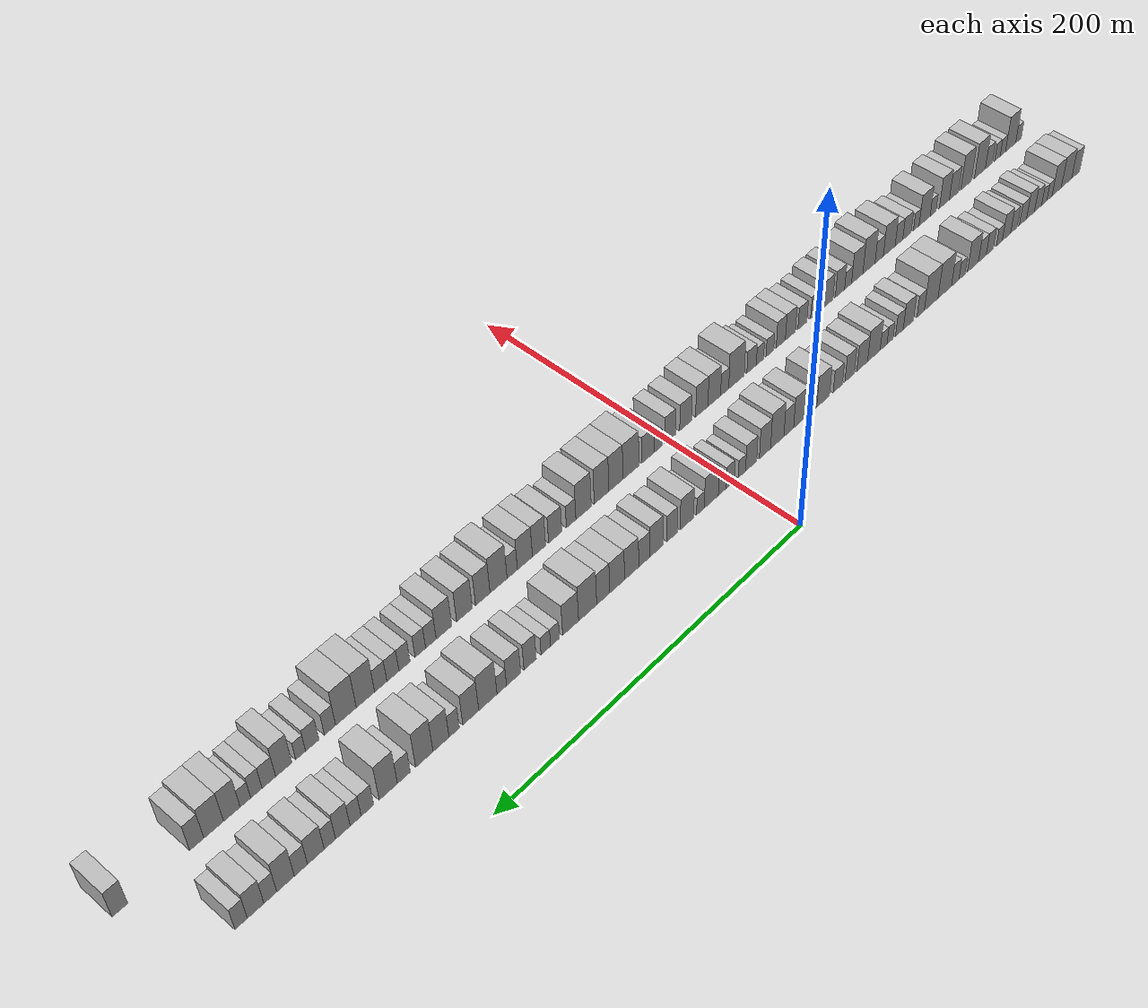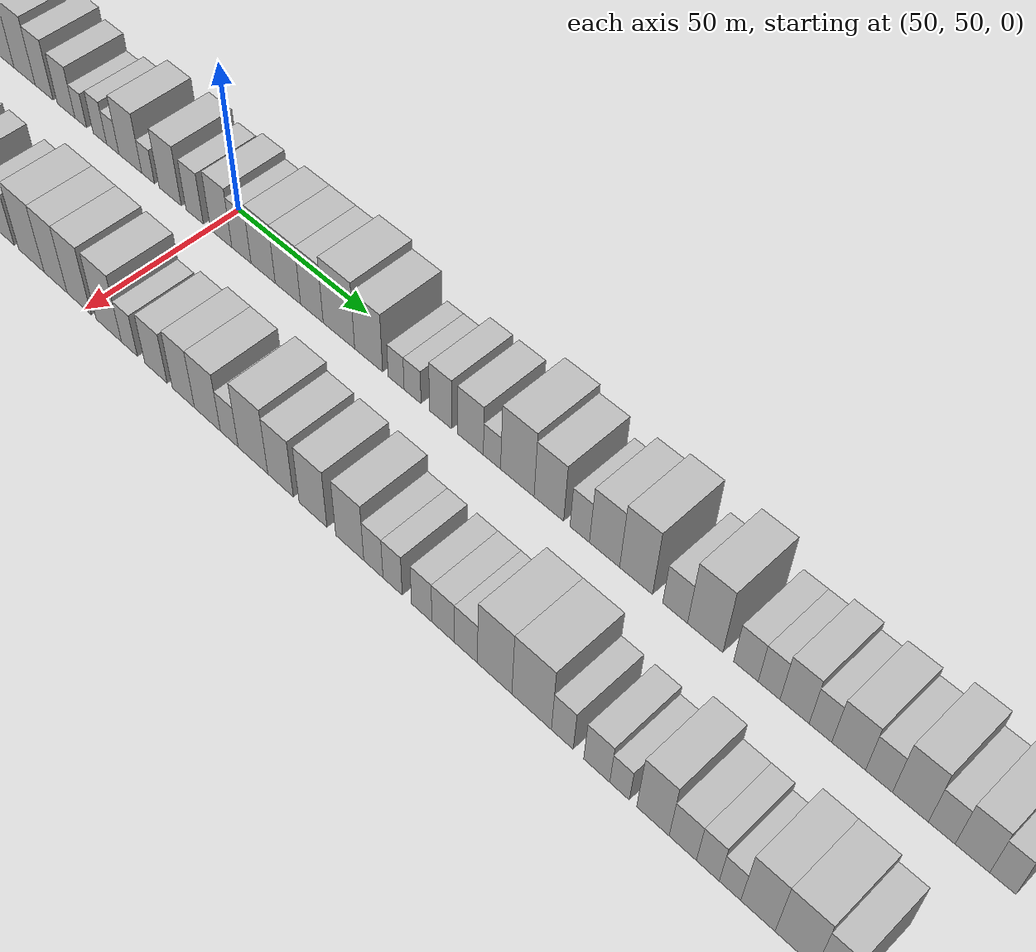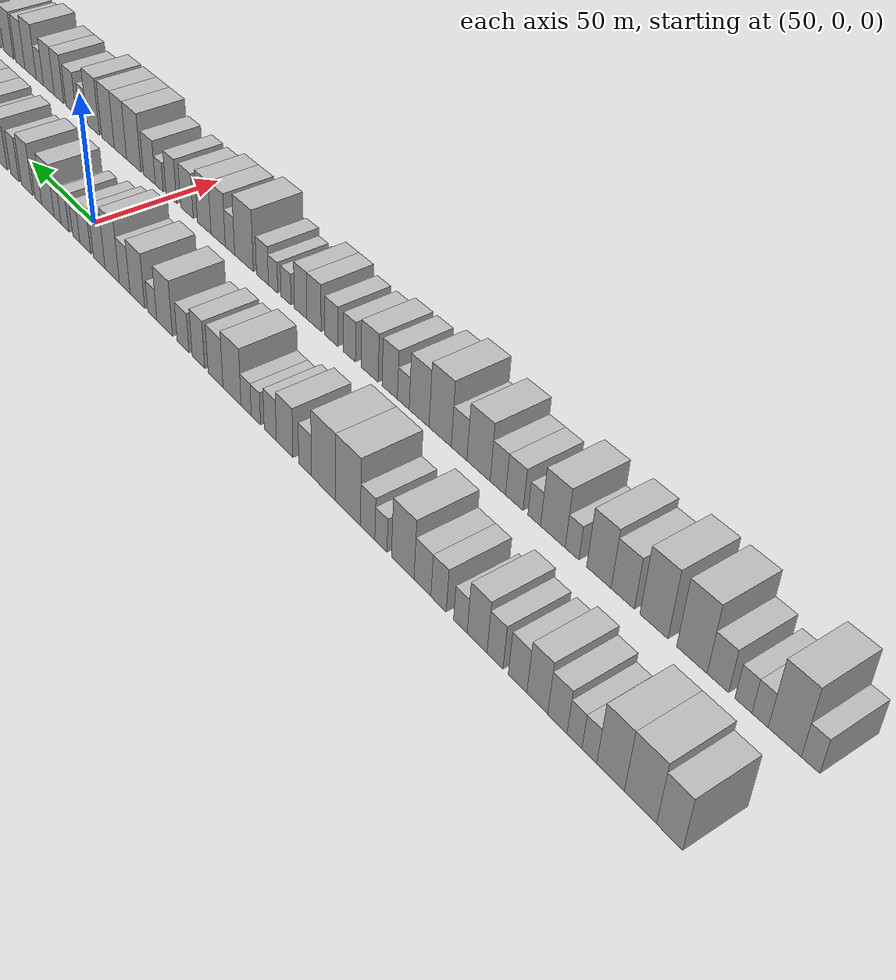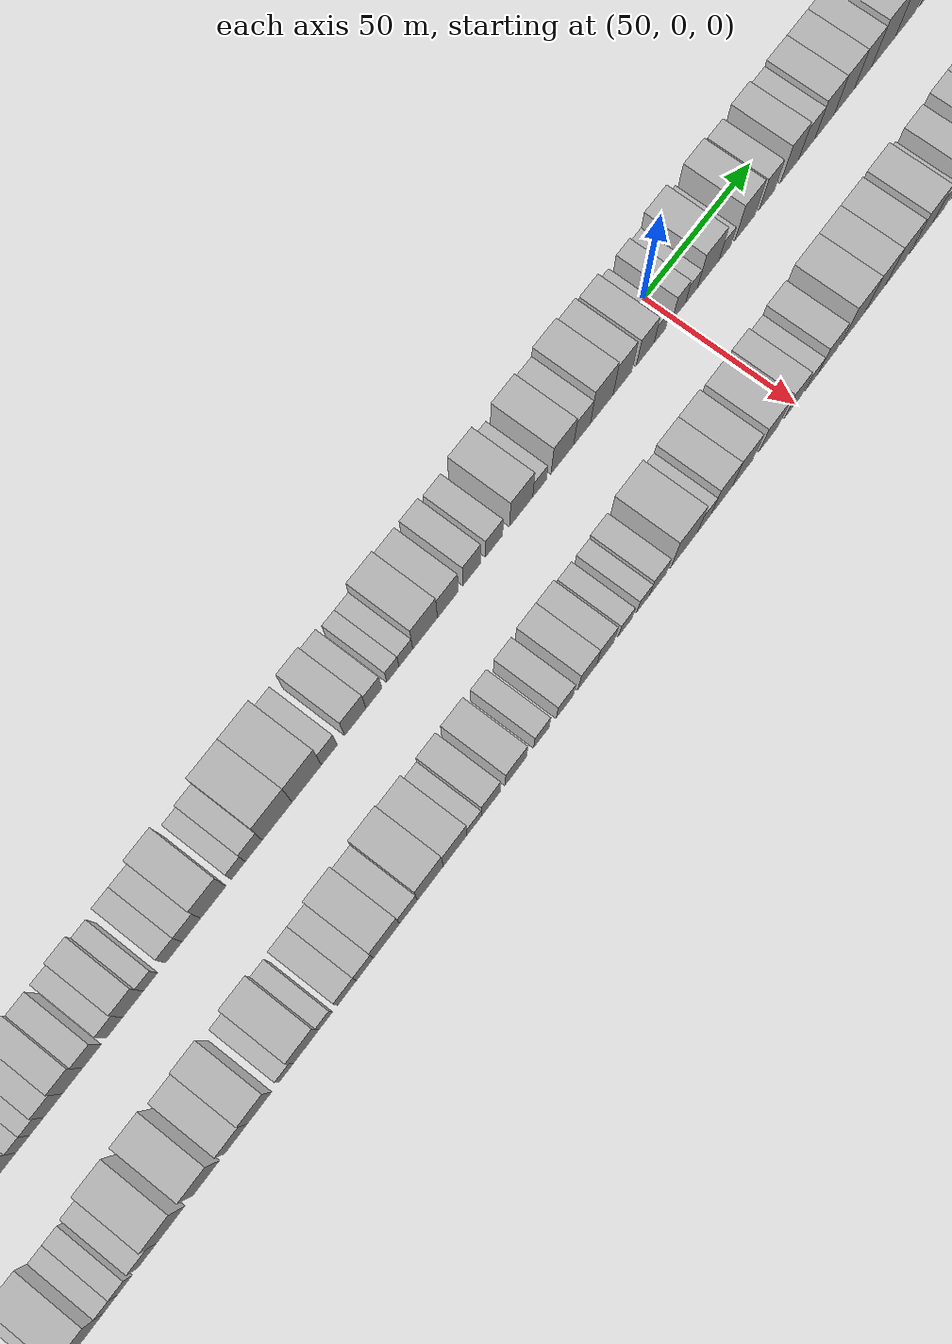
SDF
<sdf version="1.6">
 <world name="default">
  <scene>
   <sky><clouds><speed>12</speed></clouds></sky>
   <ambient>0.4 0.4 0.4 1</ambient>
   <background>0.7 0.7 0.7 1</background>
   <shadows>1</shadows>
  </scene>
  <gravity>0 0 -9.8066</gravity>
  <magnetic_field>6e-06 2.3e-05 -4.2e-05</magnetic_field>
  <physics default="0" name="default_physics" type="ode">
   <ode>
    <solver>
     <type>quick</type>
     <iters>10</iters>
     <sor>1.0</sor>
     <use_dynamic_moi_rescaling>0</use_dynamic_moi_rescaling>
    </solver>
    <constraints>
     <cfm>0</cfm>
     <erp>0.2</erp>
     <contact_max_correcting_vel>100</contact_max_correcting_vel>
     <contact_surface_layer>0.001</contact_surface_layer>
    </constraints>
   </ode>
   <max_step_size>0.004</max_step_size>
   <real_time_factor>1</real_time_factor>
   <real_time_update_rate>250</real_time_update_rate>
  </physics>
  <light name="sun" type="directional">
   <pose>0 0 10 0 0 0</pose>
   <diffuse>0.8 0.8 0.8 1</diffuse>
   <specular>0.2 0.2 0.2 1</specular>
   <attenuation>
    <range>1000</range>
    <constant>0.9</constant>
    <linear>0.01</linear>
    <quadratic>0.001</quadratic>
   </attenuation>
   <direction>-0.5 0.1 -0.9</direction>
  </light>
  <model name="building_1">
   <static>1</static>
   <pose>50.0000 -292.9607 0 0.000000 0.000000 0.000000</pose>
   <link name="link">
    <pose>0 0 9.00 0 0 0</pose>
    <collision name="collision"><geometry><box><size>20.0000 8.0786 18.0000</size></box></geometry></collision>
    <visual name="visual">
     <cast_shadows>0</cast_shadows>
     <geometry><box><size>20.0000 8.0786 18.0000</size></box></geometry>
     <material>
      <script>
       <uri>model://HANNAS_wall/materials/scripts</uri>
       <uri>model://HANNAS_wall/materials/textures</uri>
       <name>vrc/HANNAS_wall</name>
      </script>
     </material>
    </visual>
   </link>
  </model>
  <model name="building_2">
   <static>1</static>
   <pose>50.0000 -283.7995 0 0.000000 0.000000 0.000000</pose>
   <link name="link">
    <pose>0 0 10.50 0 0 0</pose>
    <collision name="collision"><geometry><box><size>20.0000 10.2437 21.0000</size></box></geometry></collision>
    <visual name="visual">
     <cast_shadows>0</cast_shadows>
     <geometry><box><size>20.0000 10.2437 21.0000</size></box></geometry>
     <material>
      <script>
       <uri>model://HANNAS_wall/materials/scripts</uri>
       <uri>model://HANNAS_wall/materials/textures</uri>
       <name>vrc/HANNAS_wall</name>
      </script>
     </material>
    </visual>
   </link>
  </model>
  <model name="building_3">
   <static>1</static>
   <pose>50.0000 -274.1064 0 0.000000 0.000000 0.000000</pose>
   <link name="link">
    <pose>0 0 10.50 0 0 0</pose>
    <collision name="collision"><geometry><box><size>20.0000 9.1425 21.0000</size></box></geometry></collision>
    <visual name="visual">
     <cast_shadows>0</cast_shadows>
     <geometry><box><size>20.0000 9.1425 21.0000</size></box></geometry>
     <material>
      <script>
       <uri>model://HANNAS_wall/materials/scripts</uri>
       <uri>model://HANNAS_wall/materials/textures</uri>
       <name>vrc/HANNAS_wall</name>
      </script>
     </material>
    </visual>
   </link>
  </model>
  <model name="building_4">
   <static>1</static>
   <pose>50.0000 -267.0367 0 0.000000 0.000000 0.000000</pose>
   <link name="link">
    <pose>0 0 6.00 0 0 0</pose>
    <collision name="collision"><geometry><box><size>20.0000 4.9970 12.0000</size></box></geometry></collision>
    <visual name="visual">
     <cast_shadows>0</cast_shadows>
     <geometry><box><size>20.0000 4.9970 12.0000</size></box></geometry>
     <material>
      <script>
       <uri>model://HANNAS_wall/materials/scripts</uri>
       <uri>model://HANNAS_wall/materials/textures</uri>
       <name>vrc/HANNAS_wall</name>
      </script>
     </material>
    </visual>
   </link>
  </model>
  <model name="building_5">
   <static>1</static>
   <pose>50.0000 -261.9520 0 0.000000 0.000000 0.000000</pose>
   <link name="link">
    <pose>0 0 6.00 0 0 0</pose>
    <collision name="collision"><geometry><box><size>20.0000 5.1724 12.0000</size></box></geometry></collision>
    <visual name="visual">
     <cast_shadows>0</cast_shadows>
     <geometry><box><size>20.0000 5.1724 12.0000</size></box></geometry>
     <material>
      <script>
       <uri>model://HANNAS_wall/materials/scripts</uri>
       <uri>model://HANNAS_wall/materials/textures</uri>
       <name>vrc/HANNAS_wall</name>
      </script>
     </material>
    </visual>
   </link>
  </model>
  <model name="building_6">
   <static>1</static>
   <pose>50.0000 -255.9389 0 0.000000 0.000000 0.000000</pose>
   <link name="link">
    <pose>0 0 7.50 0 0 0</pose>
    <collision name="collision"><geometry><box><size>20.0000 6.8538 15.0000</size></box></geometry></collision>
    <visual name="visual">
     <cast_shadows>0</cast_shadows>
     <geometry><box><size>20.0000 6.8538 15.0000</size></box></geometry>
     <material>
      <script>
       <uri>model://HANNAS_wall/materials/scripts</uri>
       <uri>model://HANNAS_wall/materials/textures</uri>
       <name>vrc/HANNAS_wall</name>
      </script>
     </material>
    </visual>
   </link>
  </model>
  <model name="building_7">
   <static>1</static>
   <pose>50.0000 -248.7187 0 0.000000 0.000000 0.000000</pose>
   <link name="link">
    <pose>0 0 9.00 0 0 0</pose>
    <collision name="collision"><geometry><box><size>20.0000 7.5866 18.0000</size></box></geometry></collision>
    <visual name="visual">
     <cast_shadows>0</cast_shadows>
     <geometry><box><size>20.0000 7.5866 18.0000</size></box></geometry>
     <material>
      <script>
       <uri>model://HANNAS_wall/materials/scripts</uri>
       <uri>model://HANNAS_wall/materials/textures</uri>
       <name>vrc/HANNAS_wall</name>
      </script>
     </material>
    </visual>
   </link>
  </model>
  <model name="building_8">
   <static>1</static>
   <pose>50.0000 -241.4648 0 0.000000 0.000000 0.000000</pose>
   <link name="link">
    <pose>0 0 7.50 0 0 0</pose>
    <collision name="collision"><geometry><box><size>20.0000 6.9213 15.0000</size></box></geometry></collision>
    <visual name="visual">
     <cast_shadows>0</cast_shadows>
     <geometry><box><size>20.0000 6.9213 15.0000</size></box></geometry>
     <material>
      <script>
       <uri>model://HANNAS_wall/materials/scripts</uri>
       <uri>model://HANNAS_wall/materials/textures</uri>
       <name>vrc/HANNAS_wall</name>
      </script>
     </material>
    </visual>
   </link>
  </model>
  <model name="building_9">
   <static>1</static>
   <pose>50.0000 -232.9255 0 0.000000 0.000000 0.000000</pose>
   <link name="link">
    <pose>0 0 7.50 0 0 0</pose>
    <collision name="collision"><geometry><box><size>20.0000 6.1572 15.0000</size></box></geometry></collision>
    <visual name="visual">
     <cast_shadows>0</cast_shadows>
     <geometry><box><size>20.0000 6.1572 15.0000</size></box></geometry>
     <material>
      <script>
       <uri>model://HANNAS_wall/materials/scripts</uri>
       <uri>model://HANNAS_wall/materials/textures</uri>
       <name>vrc/HANNAS_wall</name>
      </script>
     </material>
    </visual>
   </link>
  </model>
  <model name="building_10">
   <static>1</static>
   <pose>50.0000 -225.9368 0 0.000000 0.000000 0.000000</pose>
   <link name="link">
    <pose>0 0 9.00 0 0 0</pose>
    <collision name="collision"><geometry><box><size>20.0000 7.8204 18.0000</size></box></geometry></collision>
    <visual name="visual">
     <cast_shadows>0</cast_shadows>
     <geometry><box><size>20.0000 7.8204 18.0000</size></box></geometry>
     <material>
      <script>
       <uri>model://HANNAS_wall/materials/scripts</uri>
       <uri>model://HANNAS_wall/materials/textures</uri>
       <name>vrc/HANNAS_wall</name>
      </script>
     </material>
    </visual>
   </link>
  </model>
  <model name="building_11">
   <static>1</static>
   <pose>50.0000 -219.2824 0 0.000000 0.000000 0.000000</pose>
   <link name="link">
    <pose>0 0 6.00 0 0 0</pose>
    <collision name="collision"><geometry><box><size>20.0000 5.4883 12.0000</size></box></geometry></collision>
    <visual name="visual">
     <cast_shadows>0</cast_shadows>
     <geometry><box><size>20.0000 5.4883 12.0000</size></box></geometry>
     <material>
      <script>
       <uri>model://HANNAS_wall/materials/scripts</uri>
       <uri>model://HANNAS_wall/materials/textures</uri>
       <name>vrc/HANNAS_wall</name>
      </script>
     </material>
    </visual>
   </link>
  </model>
  <model name="building_12">
   <static>1</static>
   <pose>50.0000 -210.3345 0 0.000000 0.000000 0.000000</pose>
   <link name="link">
    <pose>0 0 7.50 0 0 0</pose>
    <collision name="collision"><geometry><box><size>20.0000 6.4076 15.0000</size></box></geometry></collision>
    <visual name="visual">
     <cast_shadows>0</cast_shadows>
     <geometry><box><size>20.0000 6.4076 15.0000</size></box></geometry>
     <material>
      <script>
       <uri>model://HANNAS_wall/materials/scripts</uri>
       <uri>model://HANNAS_wall/materials/textures</uri>
       <name>vrc/HANNAS_wall</name>
      </script>
     </material>
    </visual>
   </link>
  </model>
  <model name="building_13">
   <static>1</static>
   <pose>50.0000 -203.5243 0 0.000000 0.000000 0.000000</pose>
   <link name="link">
    <pose>0 0 7.50 0 0 0</pose>
    <collision name="collision"><geometry><box><size>20.0000 7.2128 15.0000</size></box></geometry></collision>
    <visual name="visual">
     <cast_shadows>0</cast_shadows>
     <geometry><box><size>20.0000 7.2128 15.0000</size></box></geometry>
     <material>
      <script>
       <uri>model://HANNAS_wall/materials/scripts</uri>
       <uri>model://HANNAS_wall/materials/textures</uri>
       <name>vrc/HANNAS_wall</name>
      </script>
     </material>
    </visual>
   </link>
  </model>
  <model name="building_14">
   <static>1</static>
   <pose>50.0000 -194.9490 0 0.000000 0.000000 0.000000</pose>
   <link name="link">
    <pose>0 0 10.50 0 0 0</pose>
    <collision name="collision"><geometry><box><size>20.0000 9.9377 21.0000</size></box></geometry></collision>
    <visual name="visual">
     <cast_shadows>0</cast_shadows>
     <geometry><box><size>20.0000 9.9377 21.0000</size></box></geometry>
     <material>
      <script>
       <uri>model://HANNAS_wall/materials/scripts</uri>
       <uri>model://HANNAS_wall/materials/textures</uri>
       <name>vrc/HANNAS_wall</name>
      </script>
     </material>
    </visual>
   </link>
  </model>
  <model name="building_15">
   <static>1</static>
   <pose>50.0000 -185.2317 0 0.000000 0.000000 0.000000</pose>
   <link name="link">
    <pose>0 0 6.00 0 0 0</pose>
    <collision name="collision"><geometry><box><size>20.0000 5.4968 12.0000</size></box></geometry></collision>
    <visual name="visual">
     <cast_shadows>0</cast_shadows>
     <geometry><box><size>20.0000 5.4968 12.0000</size></box></geometry>
     <material>
      <script>
       <uri>model://HANNAS_wall/materials/scripts</uri>
       <uri>model://HANNAS_wall/materials/textures</uri>
       <name>vrc/HANNAS_wall</name>
      </script>
     </material>
    </visual>
   </link>
  </model>
  <model name="building_16">
   <static>1</static>
   <pose>50.0000 -179.1196 0 0.000000 0.000000 0.000000</pose>
   <link name="link">
    <pose>0 0 7.50 0 0 0</pose>
    <collision name="collision"><geometry><box><size>20.0000 6.7274 15.0000</size></box></geometry></collision>
    <visual name="visual">
     <cast_shadows>0</cast_shadows>
     <geometry><box><size>20.0000 6.7274 15.0000</size></box></geometry>
     <material>
      <script>
       <uri>model://HANNAS_wall/materials/scripts</uri>
       <uri>model://HANNAS_wall/materials/textures</uri>
       <name>vrc/HANNAS_wall</name>
      </script>
     </material>
    </visual>
   </link>
  </model>
  <model name="building_17">
   <static>1</static>
   <pose>50.0000 -169.7730 0 0.000000 0.000000 0.000000</pose>
   <link name="link">
    <pose>0 0 12.00 0 0 0</pose>
    <collision name="collision"><geometry><box><size>20.0000 11.9657 24.0000</size></box></geometry></collision>
    <visual name="visual">
     <cast_shadows>0</cast_shadows>
     <geometry><box><size>20.0000 11.9657 24.0000</size></box></geometry>
     <material>
      <script>
       <uri>model://HANNAS_wall/materials/scripts</uri>
       <uri>model://HANNAS_wall/materials/textures</uri>
       <name>vrc/HANNAS_wall</name>
      </script>
     </material>
    </visual>
   </link>
  </model>
  <model name="building_18">
   <static>1</static>
   <pose>50.0000 -157.8910 0 0.000000 0.000000 0.000000</pose>
   <link name="link">
    <pose>0 0 12.00 0 0 0</pose>
    <collision name="collision"><geometry><box><size>20.0000 11.7985 24.0000</size></box></geometry></collision>
    <visual name="visual">
     <cast_shadows>0</cast_shadows>
     <geometry><box><size>20.0000 11.7985 24.0000</size></box></geometry>
     <material>
      <script>
       <uri>model://HANNAS_wall/materials/scripts</uri>
       <uri>model://HANNAS_wall/materials/textures</uri>
       <name>vrc/HANNAS_wall</name>
      </script>
     </material>
    </visual>
   </link>
  </model>
  <model name="building_19">
   <static>1</static>
   <pose>50.0000 -148.7655 0 0.000000 0.000000 0.000000</pose>
   <link name="link">
    <pose>0 0 7.50 0 0 0</pose>
    <collision name="collision"><geometry><box><size>20.0000 6.4524 15.0000</size></box></geometry></collision>
    <visual name="visual">
     <cast_shadows>0</cast_shadows>
     <geometry><box><size>20.0000 6.4524 15.0000</size></box></geometry>
     <material>
      <script>
       <uri>model://HANNAS_wall/materials/scripts</uri>
       <uri>model://HANNAS_wall/materials/textures</uri>
       <name>vrc/HANNAS_wall</name>
      </script>
     </material>
    </visual>
   </link>
  </model>
  <model name="building_20">
   <static>1</static>
   <pose>50.0000 -138.1742 0 0.000000 0.000000 0.000000</pose>
   <link name="link">
    <pose>0 0 9.00 0 0 0</pose>
    <collision name="collision"><geometry><box><size>20.0000 8.7303 18.0000</size></box></geometry></collision>
    <visual name="visual">
     <cast_shadows>0</cast_shadows>
     <geometry><box><size>20.0000 8.7303 18.0000</size></box></geometry>
     <material>
      <script>
       <uri>model://HANNAS_wall/materials/scripts</uri>
       <uri>model://HANNAS_wall/materials/textures</uri>
       <name>vrc/HANNAS_wall</name>
      </script>
     </material>
    </visual>
   </link>
  </model>
  <model name="building_21">
   <static>1</static>
   <pose>50.0000 -130.5213 0 0.000000 0.000000 0.000000</pose>
   <link name="link">
    <pose>0 0 7.50 0 0 0</pose>
    <collision name="collision"><geometry><box><size>20.0000 6.5754 15.0000</size></box></geometry></collision>
    <visual name="visual">
     <cast_shadows>0</cast_shadows>
     <geometry><box><size>20.0000 6.5754 15.0000</size></box></geometry>
     <material>
      <script>
       <uri>model://HANNAS_wall/materials/scripts</uri>
       <uri>model://HANNAS_wall/materials/textures</uri>
       <name>vrc/HANNAS_wall</name>
      </script>
     </material>
    </visual>
   </link>
  </model>
  <model name="building_22">
   <static>1</static>
   <pose>50.0000 -122.6675 0 0.000000 0.000000 0.000000</pose>
   <link name="link">
    <pose>0 0 6.00 0 0 0</pose>
    <collision name="collision"><geometry><box><size>20.0000 5.1323 12.0000</size></box></geometry></collision>
    <visual name="visual">
     <cast_shadows>0</cast_shadows>
     <geometry><box><size>20.0000 5.1323 12.0000</size></box></geometry>
     <material>
      <script>
       <uri>model://HANNAS_wall/materials/scripts</uri>
       <uri>model://HANNAS_wall/materials/textures</uri>
       <name>vrc/HANNAS_wall</name>
      </script>
     </material>
    </visual>
   </link>
  </model>
  <model name="building_23">
   <static>1</static>
   <pose>50.0000 -117.2452 0 0.000000 0.000000 0.000000</pose>
   <link name="link">
    <pose>0 0 6.00 0 0 0</pose>
    <collision name="collision"><geometry><box><size>20.0000 5.7124 12.0000</size></box></geometry></collision>
    <visual name="visual">
     <cast_shadows>0</cast_shadows>
     <geometry><box><size>20.0000 5.7124 12.0000</size></box></geometry>
     <material>
      <script>
       <uri>model://HANNAS_wall/materials/scripts</uri>
       <uri>model://HANNAS_wall/materials/textures</uri>
       <name>vrc/HANNAS_wall</name>
      </script>
     </material>
    </visual>
   </link>
  </model>
  <model name="building_24">
   <static>1</static>
   <pose>50.0000 -109.2051 0 0.000000 0.000000 0.000000</pose>
   <link name="link">
    <pose>0 0 10.50 0 0 0</pose>
    <collision name="collision"><geometry><box><size>20.0000 10.3678 21.0000</size></box></geometry></collision>
    <visual name="visual">
     <cast_shadows>0</cast_shadows>
     <geometry><box><size>20.0000 10.3678 21.0000</size></box></geometry>
     <material>
      <script>
       <uri>model://HANNAS_wall/materials/scripts</uri>
       <uri>model://HANNAS_wall/materials/textures</uri>
       <name>vrc/HANNAS_wall</name>
      </script>
     </material>
    </visual>
   </link>
  </model>
  <model name="building_25">
   <static>1</static>
   <pose>50.0000 -99.6082 0 0.000000 0.000000 0.000000</pose>
   <link name="link">
    <pose>0 0 9.00 0 0 0</pose>
    <collision name="collision"><geometry><box><size>20.0000 8.8259 18.0000</size></box></geometry></collision>
    <visual name="visual">
     <cast_shadows>0</cast_shadows>
     <geometry><box><size>20.0000 8.8259 18.0000</size></box></geometry>
     <material>
      <script>
       <uri>model://HANNAS_wall/materials/scripts</uri>
       <uri>model://HANNAS_wall/materials/textures</uri>
       <name>vrc/HANNAS_wall</name>
      </script>
     </material>
    </visual>
   </link>
  </model>
  <model name="building_26">
   <static>1</static>
   <pose>50.0000 -89.3724 0 0.000000 0.000000 0.000000</pose>
   <link name="link">
    <pose>0 0 9.00 0 0 0</pose>
    <collision name="collision"><geometry><box><size>20.0000 7.6458 18.0000</size></box></geometry></collision>
    <visual name="visual">
     <cast_shadows>0</cast_shadows>
     <geometry><box><size>20.0000 7.6458 18.0000</size></box></geometry>
     <material>
      <script>
       <uri>model://HANNAS_wall/materials/scripts</uri>
       <uri>model://HANNAS_wall/materials/textures</uri>
       <name>vrc/HANNAS_wall</name>
      </script>
     </material>
    </visual>
   </link>
  </model>
  <model name="building_27">
   <static>1</static>
   <pose>50.0000 -79.8591 0 0.000000 0.000000 0.000000</pose>
   <link name="link">
    <pose>0 0 7.50 0 0 0</pose>
    <collision name="collision"><geometry><box><size>20.0000 7.3808 15.0000</size></box></geometry></collision>
    <visual name="visual">
     <cast_shadows>0</cast_shadows>
     <geometry><box><size>20.0000 7.3808 15.0000</size></box></geometry>
     <material>
      <script>
       <uri>model://HANNAS_wall/materials/scripts</uri>
       <uri>model://HANNAS_wall/materials/textures</uri>
       <name>vrc/HANNAS_wall</name>
      </script>
     </material>
    </visual>
   </link>
  </model>
  <model name="building_28">
   <static>1</static>
   <pose>50.0000 -68.1175 0 0.000000 0.000000 0.000000</pose>
   <link name="link">
    <pose>0 0 10.50 0 0 0</pose>
    <collision name="collision"><geometry><box><size>20.0000 10.1024 21.0000</size></box></geometry></collision>
    <visual name="visual">
     <cast_shadows>0</cast_shadows>
     <geometry><box><size>20.0000 10.1024 21.0000</size></box></geometry>
     <material>
      <script>
       <uri>model://HANNAS_wall/materials/scripts</uri>
       <uri>model://HANNAS_wall/materials/textures</uri>
       <name>vrc/HANNAS_wall</name>
      </script>
     </material>
    </visual>
   </link>
  </model>
  <model name="building_29">
   <static>1</static>
   <pose>50.0000 -60.0794 0 0.000000 0.000000 0.000000</pose>
   <link name="link">
    <pose>0 0 6.00 0 0 0</pose>
    <collision name="collision"><geometry><box><size>20.0000 5.9738 12.0000</size></box></geometry></collision>
    <visual name="visual">
     <cast_shadows>0</cast_shadows>
     <geometry><box><size>20.0000 5.9738 12.0000</size></box></geometry>
     <material>
      <script>
       <uri>model://HANNAS_wall/materials/scripts</uri>
       <uri>model://HANNAS_wall/materials/textures</uri>
       <name>vrc/HANNAS_wall</name>
      </script>
     </material>
    </visual>
   </link>
  </model>
  <model name="building_30">
   <static>1</static>
   <pose>50.0000 -50.0860 0 0.000000 0.000000 0.000000</pose>
   <link name="link">
    <pose>0 0 10.50 0 0 0</pose>
    <collision name="collision"><geometry><box><size>20.0000 10.0130 21.0000</size></box></geometry></collision>
    <visual name="visual">
     <cast_shadows>0</cast_shadows>
     <geometry><box><size>20.0000 10.0130 21.0000</size></box></geometry>
     <material>
      <script>
       <uri>model://HANNAS_wall/materials/scripts</uri>
       <uri>model://HANNAS_wall/materials/textures</uri>
       <name>vrc/HANNAS_wall</name>
      </script>
     </material>
    </visual>
   </link>
  </model>
  <model name="building_31">
   <static>1</static>
   <pose>50.0000 -41.3721 0 0.000000 0.000000 0.000000</pose>
   <link name="link">
    <pose>0 0 9.00 0 0 0</pose>
    <collision name="collision"><geometry><box><size>20.0000 7.4148 18.0000</size></box></geometry></collision>
    <visual name="visual">
     <cast_shadows>0</cast_shadows>
     <geometry><box><size>20.0000 7.4148 18.0000</size></box></geometry>
     <material>
      <script>
       <uri>model://HANNAS_wall/materials/scripts</uri>
       <uri>model://HANNAS_wall/materials/textures</uri>
       <name>vrc/HANNAS_wall</name>
      </script>
     </material>
    </visual>
   </link>
  </model>
  <model name="building_32">
   <static>1</static>
   <pose>50.0000 -32.5783 0 0.000000 0.000000 0.000000</pose>
   <link name="link">
    <pose>0 0 12.00 0 0 0</pose>
    <collision name="collision"><geometry><box><size>20.0000 10.1729 24.0000</size></box></geometry></collision>
    <visual name="visual">
     <cast_shadows>0</cast_shadows>
     <geometry><box><size>20.0000 10.1729 24.0000</size></box></geometry>
     <material>
      <script>
       <uri>model://HANNAS_wall/materials/scripts</uri>
       <uri>model://HANNAS_wall/materials/textures</uri>
       <name>vrc/HANNAS_wall</name>
      </script>
     </material>
    </visual>
   </link>
  </model>
  <model name="building_33">
   <static>1</static>
   <pose>50.0000 -23.2700 0 0.000000 0.000000 0.000000</pose>
   <link name="link">
    <pose>0 0 10.50 0 0 0</pose>
    <collision name="collision"><geometry><box><size>20.0000 8.4438 21.0000</size></box></geometry></collision>
    <visual name="visual">
     <cast_shadows>0</cast_shadows>
     <geometry><box><size>20.0000 8.4438 21.0000</size></box></geometry>
     <material>
      <script>
       <uri>model://HANNAS_wall/materials/scripts</uri>
       <uri>model://HANNAS_wall/materials/textures</uri>
       <name>vrc/HANNAS_wall</name>
      </script>
     </material>
    </visual>
   </link>
  </model>
  <model name="building_34">
   <static>1</static>
   <pose>50.0000 -12.9507 0 0.000000 0.000000 0.000000</pose>
   <link name="link">
    <pose>0 0 9.00 0 0 0</pose>
    <collision name="collision"><geometry><box><size>20.0000 8.1948 18.0000</size></box></geometry></collision>
    <visual name="visual">
     <cast_shadows>0</cast_shadows>
     <geometry><box><size>20.0000 8.1948 18.0000</size></box></geometry>
     <material>
      <script>
       <uri>model://HANNAS_wall/materials/scripts</uri>
       <uri>model://HANNAS_wall/materials/textures</uri>
       <name>vrc/HANNAS_wall</name>
      </script>
     </material>
    </visual>
   </link>
  </model>
  <model name="building_35">
   <static>1</static>
   <pose>50.0000 -6.1831 0 0.000000 0.000000 0.000000</pose>
   <link name="link">
    <pose>0 0 6.00 0 0 0</pose>
    <collision name="collision"><geometry><box><size>20.0000 5.3404 12.0000</size></box></geometry></collision>
    <visual name="visual">
     <cast_shadows>0</cast_shadows>
     <geometry><box><size>20.0000 5.3404 12.0000</size></box></geometry>
     <material>
      <script>
       <uri>model://HANNAS_wall/materials/scripts</uri>
       <uri>model://HANNAS_wall/materials/textures</uri>
       <name>vrc/HANNAS_wall</name>
      </script>
     </material>
    </visual>
   </link>
  </model>
  <model name="building_36">
   <static>1</static>
   <pose>50.0000 2.5396 0 0.000000 0.000000 0.000000</pose>
   <link name="link">
    <pose>0 0 7.50 0 0 0</pose>
    <collision name="collision"><geometry><box><size>20.0000 6.1050 15.0000</size></box></geometry></collision>
    <visual name="visual">
     <cast_shadows>0</cast_shadows>
     <geometry><box><size>20.0000 6.1050 15.0000</size></box></geometry>
     <material>
      <script>
       <uri>model://HANNAS_wall/materials/scripts</uri>
       <uri>model://HANNAS_wall/materials/textures</uri>
       <name>vrc/HANNAS_wall</name>
      </script>
     </material>
    </visual>
   </link>
  </model>
  <model name="building_37">
   <static>1</static>
   <pose>50.0000 8.3543 0 0.000000 0.000000 0.000000</pose>
   <link name="link">
    <pose>0 0 6.00 0 0 0</pose>
    <collision name="collision"><geometry><box><size>20.0000 5.5245 12.0000</size></box></geometry></collision>
    <visual name="visual">
     <cast_shadows>0</cast_shadows>
     <geometry><box><size>20.0000 5.5245 12.0000</size></box></geometry>
     <material>
      <script>
       <uri>model://HANNAS_wall/materials/scripts</uri>
       <uri>model://HANNAS_wall/materials/textures</uri>
       <name>vrc/HANNAS_wall</name>
      </script>
     </material>
    </visual>
   </link>
  </model>
  <model name="building_38">
   <static>1</static>
   <pose>50.0000 16.1037 0 0.000000 0.000000 0.000000</pose>
   <link name="link">
    <pose>0 0 10.50 0 0 0</pose>
    <collision name="collision"><geometry><box><size>20.0000 9.9742 21.0000</size></box></geometry></collision>
    <visual name="visual">
     <cast_shadows>0</cast_shadows>
     <geometry><box><size>20.0000 9.9742 21.0000</size></box></geometry>
     <material>
      <script>
       <uri>model://HANNAS_wall/materials/scripts</uri>
       <uri>model://HANNAS_wall/materials/textures</uri>
       <name>vrc/HANNAS_wall</name>
      </script>
     </material>
    </visual>
   </link>
  </model>
  <model name="building_39">
   <static>1</static>
   <pose>50.0000 23.8589 0 0.000000 0.000000 0.000000</pose>
   <link name="link">
    <pose>0 0 6.00 0 0 0</pose>
    <collision name="collision"><geometry><box><size>20.0000 5.5364 12.0000</size></box></geometry></collision>
    <visual name="visual">
     <cast_shadows>0</cast_shadows>
     <geometry><box><size>20.0000 5.5364 12.0000</size></box></geometry>
     <material>
      <script>
       <uri>model://HANNAS_wall/materials/scripts</uri>
       <uri>model://HANNAS_wall/materials/textures</uri>
       <name>vrc/HANNAS_wall</name>
      </script>
     </material>
    </visual>
   </link>
  </model>
  <model name="building_40">
   <static>1</static>
   <pose>50.0000 33.3413 0 0.000000 0.000000 0.000000</pose>
   <link name="link">
    <pose>0 0 10.50 0 0 0</pose>
    <collision name="collision"><geometry><box><size>20.0000 9.4282 21.0000</size></box></geometry></collision>
    <visual name="visual">
     <cast_shadows>0</cast_shadows>
     <geometry><box><size>20.0000 9.4282 21.0000</size></box></geometry>
     <material>
      <script>
       <uri>model://HANNAS_wall/materials/scripts</uri>
       <uri>model://HANNAS_wall/materials/textures</uri>
       <name>vrc/HANNAS_wall</name>
      </script>
     </material>
    </visual>
   </link>
  </model>
  <model name="building_41">
   <static>1</static>
   <pose>50.0000 43.6738 0 0.000000 0.000000 0.000000</pose>
   <link name="link">
    <pose>0 0 9.00 0 0 0</pose>
    <collision name="collision"><geometry><box><size>20.0000 7.2368 18.0000</size></box></geometry></collision>
    <visual name="visual">
     <cast_shadows>0</cast_shadows>
     <geometry><box><size>20.0000 7.2368 18.0000</size></box></geometry>
     <material>
      <script>
       <uri>model://HANNAS_wall/materials/scripts</uri>
       <uri>model://HANNAS_wall/materials/textures</uri>
       <name>vrc/HANNAS_wall</name>
      </script>
     </material>
    </visual>
   </link>
  </model>
  <model name="building_42">
   <static>1</static>
   <pose>50.0000 54.6382 0 0.000000 0.000000 0.000000</pose>
   <link name="link">
    <pose>0 0 10.50 0 0 0</pose>
    <collision name="collision"><geometry><box><size>20.0000 8.6921 21.0000</size></box></geometry></collision>
    <visual name="visual">
     <cast_shadows>0</cast_shadows>
     <geometry><box><size>20.0000 8.6921 21.0000</size></box></geometry>
     <material>
      <script>
       <uri>model://HANNAS_wall/materials/scripts</uri>
       <uri>model://HANNAS_wall/materials/textures</uri>
       <name>vrc/HANNAS_wall</name>
      </script>
     </material>
    </visual>
   </link>
  </model>
  <model name="building_43">
   <static>1</static>
   <pose>50.0000 62.8460 0 0.000000 0.000000 0.000000</pose>
   <link name="link">
    <pose>0 0 9.00 0 0 0</pose>
    <collision name="collision"><geometry><box><size>20.0000 7.7234 18.0000</size></box></geometry></collision>
    <visual name="visual">
     <cast_shadows>0</cast_shadows>
     <geometry><box><size>20.0000 7.7234 18.0000</size></box></geometry>
     <material>
      <script>
       <uri>model://HANNAS_wall/materials/scripts</uri>
       <uri>model://HANNAS_wall/materials/textures</uri>
       <name>vrc/HANNAS_wall</name>
      </script>
     </material>
    </visual>
   </link>
  </model>
  <model name="building_44">
   <static>1</static>
   <pose>50.0000 71.4762 0 0.000000 0.000000 0.000000</pose>
   <link name="link">
    <pose>0 0 10.50 0 0 0</pose>
    <collision name="collision"><geometry><box><size>20.0000 9.5371 21.0000</size></box></geometry></collision>
    <visual name="visual">
     <cast_shadows>0</cast_shadows>
     <geometry><box><size>20.0000 9.5371 21.0000</size></box></geometry>
     <material>
      <script>
       <uri>model://HANNAS_wall/materials/scripts</uri>
       <uri>model://HANNAS_wall/materials/textures</uri>
       <name>vrc/HANNAS_wall</name>
      </script>
     </material>
    </visual>
   </link>
  </model>
  <model name="building_45">
   <static>1</static>
   <pose>50.0000 81.1672 0 0.000000 0.000000 0.000000</pose>
   <link name="link">
    <pose>0 0 10.50 0 0 0</pose>
    <collision name="collision"><geometry><box><size>20.0000 9.8448 21.0000</size></box></geometry></collision>
    <visual name="visual">
     <cast_shadows>0</cast_shadows>
     <geometry><box><size>20.0000 9.8448 21.0000</size></box></geometry>
     <material>
      <script>
       <uri>model://HANNAS_wall/materials/scripts</uri>
       <uri>model://HANNAS_wall/materials/textures</uri>
       <name>vrc/HANNAS_wall</name>
      </script>
     </material>
    </visual>
   </link>
  </model>
  <model name="building_46">
   <static>1</static>
   <pose>50.0000 90.3996 0 0.000000 0.000000 0.000000</pose>
   <link name="link">
    <pose>0 0 10.50 0 0 0</pose>
    <collision name="collision"><geometry><box><size>20.0000 8.6202 21.0000</size></box></geometry></collision>
    <visual name="visual">
     <cast_shadows>0</cast_shadows>
     <geometry><box><size>20.0000 8.6202 21.0000</size></box></geometry>
     <material>
      <script>
       <uri>model://HANNAS_wall/materials/scripts</uri>
       <uri>model://HANNAS_wall/materials/textures</uri>
       <name>vrc/HANNAS_wall</name>
      </script>
     </material>
    </visual>
   </link>
  </model>
  <model name="building_47">
   <static>1</static>
   <pose>50.0000 100.5778 0 0.000000 0.000000 0.000000</pose>
   <link name="link">
    <pose>0 0 12.00 0 0 0</pose>
    <collision name="collision"><geometry><box><size>20.0000 11.7363 24.0000</size></box></geometry></collision>
    <visual name="visual">
     <cast_shadows>0</cast_shadows>
     <geometry><box><size>20.0000 11.7363 24.0000</size></box></geometry>
     <material>
      <script>
       <uri>model://HANNAS_wall/materials/scripts</uri>
       <uri>model://HANNAS_wall/materials/textures</uri>
       <name>vrc/HANNAS_wall</name>
      </script>
     </material>
    </visual>
   </link>
  </model>
  <model name="building_48">
   <static>1</static>
   <pose>50.0000 111.5434 0 0.000000 0.000000 0.000000</pose>
   <link name="link">
    <pose>0 0 10.50 0 0 0</pose>
    <collision name="collision"><geometry><box><size>20.0000 10.1949 21.0000</size></box></geometry></collision>
    <visual name="visual">
     <cast_shadows>0</cast_shadows>
     <geometry><box><size>20.0000 10.1949 21.0000</size></box></geometry>
     <material>
      <script>
       <uri>model://HANNAS_wall/materials/scripts</uri>
       <uri>model://HANNAS_wall/materials/textures</uri>
       <name>vrc/HANNAS_wall</name>
      </script>
     </material>
    </visual>
   </link>
  </model>
  <model name="building_49">
   <static>1</static>
   <pose>50.0000 121.4799 0 0.000000 0.000000 0.000000</pose>
   <link name="link">
    <pose>0 0 6.00 0 0 0</pose>
    <collision name="collision"><geometry><box><size>20.0000 5.6781 12.0000</size></box></geometry></collision>
    <visual name="visual">
     <cast_shadows>0</cast_shadows>
     <geometry><box><size>20.0000 5.6781 12.0000</size></box></geometry>
     <material>
      <script>
       <uri>model://HANNAS_wall/materials/scripts</uri>
       <uri>model://HANNAS_wall/materials/textures</uri>
       <name>vrc/HANNAS_wall</name>
      </script>
     </material>
    </visual>
   </link>
  </model>
  <model name="building_50">
   <static>1</static>
   <pose>50.0000 127.2958 0 0.000000 0.000000 0.000000</pose>
   <link name="link">
    <pose>0 0 6.00 0 0 0</pose>
    <collision name="collision"><geometry><box><size>20.0000 5.9538 12.0000</size></box></geometry></collision>
    <visual name="visual">
     <cast_shadows>0</cast_shadows>
     <geometry><box><size>20.0000 5.9538 12.0000</size></box></geometry>
     <material>
      <script>
       <uri>model://HANNAS_wall/materials/scripts</uri>
       <uri>model://HANNAS_wall/materials/textures</uri>
       <name>vrc/HANNAS_wall</name>
      </script>
     </material>
    </visual>
   </link>
  </model>
  <model name="building_51">
   <static>1</static>
   <pose>50.0000 137.0834 0 0.000000 0.000000 0.000000</pose>
   <link name="link">
    <pose>0 0 9.00 0 0 0</pose>
    <collision name="collision"><geometry><box><size>20.0000 7.6214 18.0000</size></box></geometry></collision>
    <visual name="visual">
     <cast_shadows>0</cast_shadows>
     <geometry><box><size>20.0000 7.6214 18.0000</size></box></geometry>
     <material>
      <script>
       <uri>model://HANNAS_wall/materials/scripts</uri>
       <uri>model://HANNAS_wall/materials/textures</uri>
       <name>vrc/HANNAS_wall</name>
      </script>
     </material>
    </visual>
   </link>
  </model>
  <model name="building_52">
   <static>1</static>
   <pose>50.0000 147.2627 0 0.000000 0.000000 0.000000</pose>
   <link name="link">
    <pose>0 0 9.00 0 0 0</pose>
    <collision name="collision"><geometry><box><size>20.0000 8.7371 18.0000</size></box></geometry></collision>
    <visual name="visual">
     <cast_shadows>0</cast_shadows>
     <geometry><box><size>20.0000 8.7371 18.0000</size></box></geometry>
     <material>
      <script>
       <uri>model://HANNAS_wall/materials/scripts</uri>
       <uri>model://HANNAS_wall/materials/textures</uri>
       <name>vrc/HANNAS_wall</name>
      </script>
     </material>
    </visual>
   </link>
  </model>
  <model name="building_53">
   <static>1</static>
   <pose>50.0000 154.4968 0 0.000000 0.000000 0.000000</pose>
   <link name="link">
    <pose>0 0 6.00 0 0 0</pose>
    <collision name="collision"><geometry><box><size>20.0000 5.7311 12.0000</size></box></geometry></collision>
    <visual name="visual">
     <cast_shadows>0</cast_shadows>
     <geometry><box><size>20.0000 5.7311 12.0000</size></box></geometry>
     <material>
      <script>
       <uri>model://HANNAS_wall/materials/scripts</uri>
       <uri>model://HANNAS_wall/materials/textures</uri>
       <name>vrc/HANNAS_wall</name>
      </script>
     </material>
    </visual>
   </link>
  </model>
  <model name="building_54">
   <static>1</static>
   <pose>50.0000 162.8468 0 0.000000 0.000000 0.000000</pose>
   <link name="link">
    <pose>0 0 12.00 0 0 0</pose>
    <collision name="collision"><geometry><box><size>20.0000 10.9688 24.0000</size></box></geometry></collision>
    <visual name="visual">
     <cast_shadows>0</cast_shadows>
     <geometry><box><size>20.0000 10.9688 24.0000</size></box></geometry>
     <material>
      <script>
       <uri>model://HANNAS_wall/materials/scripts</uri>
       <uri>model://HANNAS_wall/materials/textures</uri>
       <name>vrc/HANNAS_wall</name>
      </script>
     </material>
    </visual>
   </link>
  </model>
  <model name="building_55">
   <static>1</static>
   <pose>50.0000 173.0609 0 0.000000 0.000000 0.000000</pose>
   <link name="link">
    <pose>0 0 10.50 0 0 0</pose>
    <collision name="collision"><geometry><box><size>20.0000 9.4594 21.0000</size></box></geometry></collision>
    <visual name="visual">
     <cast_shadows>0</cast_shadows>
     <geometry><box><size>20.0000 9.4594 21.0000</size></box></geometry>
     <material>
      <script>
       <uri>model://HANNAS_wall/materials/scripts</uri>
       <uri>model://HANNAS_wall/materials/textures</uri>
       <name>vrc/HANNAS_wall</name>
      </script>
     </material>
    </visual>
   </link>
  </model>
  <model name="building_56">
   <static>1</static>
   <pose>50.0000 182.8200 0 0.000000 0.000000 0.000000</pose>
   <link name="link">
    <pose>0 0 7.50 0 0 0</pose>
    <collision name="collision"><geometry><box><size>20.0000 6.0588 15.0000</size></box></geometry></collision>
    <visual name="visual">
     <cast_shadows>0</cast_shadows>
     <geometry><box><size>20.0000 6.0588 15.0000</size></box></geometry>
     <material>
      <script>
       <uri>model://HANNAS_wall/materials/scripts</uri>
       <uri>model://HANNAS_wall/materials/textures</uri>
       <name>vrc/HANNAS_wall</name>
      </script>
     </material>
    </visual>
   </link>
  </model>
  <model name="building_57">
   <static>1</static>
   <pose>50.0000 190.5019 0 0.000000 0.000000 0.000000</pose>
   <link name="link">
    <pose>0 0 10.50 0 0 0</pose>
    <collision name="collision"><geometry><box><size>20.0000 9.3049 21.0000</size></box></geometry></collision>
    <visual name="visual">
     <cast_shadows>0</cast_shadows>
     <geometry><box><size>20.0000 9.3049 21.0000</size></box></geometry>
     <material>
      <script>
       <uri>model://HANNAS_wall/materials/scripts</uri>
       <uri>model://HANNAS_wall/materials/textures</uri>
       <name>vrc/HANNAS_wall</name>
      </script>
     </material>
    </visual>
   </link>
  </model>
  <model name="building_58">
   <static>1</static>
   <pose>50.0000 200.1157 0 0.000000 0.000000 0.000000</pose>
   <link name="link">
    <pose>0 0 12.00 0 0 0</pose>
    <collision name="collision"><geometry><box><size>20.0000 9.9226 24.0000</size></box></geometry></collision>
    <visual name="visual">
     <cast_shadows>0</cast_shadows>
     <geometry><box><size>20.0000 9.9226 24.0000</size></box></geometry>
     <material>
      <script>
       <uri>model://HANNAS_wall/materials/scripts</uri>
       <uri>model://HANNAS_wall/materials/textures</uri>
       <name>vrc/HANNAS_wall</name>
      </script>
     </material>
    </visual>
   </link>
  </model>
  <model name="building_59">
   <static>1</static>
   <pose>50.0000 211.7154 0 0.000000 0.000000 0.000000</pose>
   <link name="link">
    <pose>0 0 7.50 0 0 0</pose>
    <collision name="collision"><geometry><box><size>20.0000 7.2768 15.0000</size></box></geometry></collision>
    <visual name="visual">
     <cast_shadows>0</cast_shadows>
     <geometry><box><size>20.0000 7.2768 15.0000</size></box></geometry>
     <material>
      <script>
       <uri>model://HANNAS_wall/materials/scripts</uri>
       <uri>model://HANNAS_wall/materials/textures</uri>
       <name>vrc/HANNAS_wall</name>
      </script>
     </material>
    </visual>
   </link>
  </model>
  <model name="building_60">
   <static>1</static>
   <pose>50.0000 220.4443 0 0.000000 0.000000 0.000000</pose>
   <link name="link">
    <pose>0 0 12.00 0 0 0</pose>
    <collision name="collision"><geometry><box><size>20.0000 10.1811 24.0000</size></box></geometry></collision>
    <visual name="visual">
     <cast_shadows>0</cast_shadows>
     <geometry><box><size>20.0000 10.1811 24.0000</size></box></geometry>
     <material>
      <script>
       <uri>model://HANNAS_wall/materials/scripts</uri>
       <uri>model://HANNAS_wall/materials/textures</uri>
       <name>vrc/HANNAS_wall</name>
      </script>
     </material>
    </visual>
   </link>
  </model>
  <model name="building_61">
   <static>1</static>
   <pose>50.0000 231.9727 0 0.000000 0.000000 0.000000</pose>
   <link name="link">
    <pose>0 0 7.50 0 0 0</pose>
    <collision name="collision"><geometry><box><size>20.0000 6.8756 15.0000</size></box></geometry></collision>
    <visual name="visual">
     <cast_shadows>0</cast_shadows>
     <geometry><box><size>20.0000 6.8756 15.0000</size></box></geometry>
     <material>
      <script>
       <uri>model://HANNAS_wall/materials/scripts</uri>
       <uri>model://HANNAS_wall/materials/textures</uri>
       <name>vrc/HANNAS_wall</name>
      </script>
     </material>
    </visual>
   </link>
  </model>
  <model name="building_62">
   <static>1</static>
   <pose>50.0000 238.4234 0 0.000000 0.000000 0.000000</pose>
   <link name="link">
    <pose>0 0 7.50 0 0 0</pose>
    <collision name="collision"><geometry><box><size>20.0000 6.0259 15.0000</size></box></geometry></collision>
    <visual name="visual">
     <cast_shadows>0</cast_shadows>
     <geometry><box><size>20.0000 6.0259 15.0000</size></box></geometry>
     <material>
      <script>
       <uri>model://HANNAS_wall/materials/scripts</uri>
       <uri>model://HANNAS_wall/materials/textures</uri>
       <name>vrc/HANNAS_wall</name>
      </script>
     </material>
    </visual>
   </link>
  </model>
  <model name="building_63">
   <static>1</static>
   <pose>50.0000 245.3792 0 0.000000 0.000000 0.000000</pose>
   <link name="link">
    <pose>0 0 9.00 0 0 0</pose>
    <collision name="collision"><geometry><box><size>20.0000 7.8857 18.0000</size></box></geometry></collision>
    <visual name="visual">
     <cast_shadows>0</cast_shadows>
     <geometry><box><size>20.0000 7.8857 18.0000</size></box></geometry>
     <material>
      <script>
       <uri>model://HANNAS_wall/materials/scripts</uri>
       <uri>model://HANNAS_wall/materials/textures</uri>
       <name>vrc/HANNAS_wall</name>
      </script>
     </material>
    </visual>
   </link>
  </model>
  <model name="building_64">
   <static>1</static>
   <pose>50.0000 252.3377 0 0.000000 0.000000 0.000000</pose>
   <link name="link">
    <pose>0 0 7.50 0 0 0</pose>
    <collision name="collision"><geometry><box><size>20.0000 6.0313 15.0000</size></box></geometry></collision>
    <visual name="visual">
     <cast_shadows>0</cast_shadows>
     <geometry><box><size>20.0000 6.0313 15.0000</size></box></geometry>
     <material>
      <script>
       <uri>model://HANNAS_wall/materials/scripts</uri>
       <uri>model://HANNAS_wall/materials/textures</uri>
       <name>vrc/HANNAS_wall</name>
      </script>
     </material>
    </visual>
   </link>
  </model>
  <model name="building_65">
   <static>1</static>
   <pose>50.0000 259.7710 0 0.000000 0.000000 0.000000</pose>
   <link name="link">
    <pose>0 0 9.00 0 0 0</pose>
    <collision name="collision"><geometry><box><size>20.0000 8.8353 18.0000</size></box></geometry></collision>
    <visual name="visual">
     <cast_shadows>0</cast_shadows>
     <geometry><box><size>20.0000 8.8353 18.0000</size></box></geometry>
     <material>
      <script>
       <uri>model://HANNAS_wall/materials/scripts</uri>
       <uri>model://HANNAS_wall/materials/textures</uri>
       <name>vrc/HANNAS_wall</name>
      </script>
     </material>
    </visual>
   </link>
  </model>
  <model name="building_66">
   <static>1</static>
   <pose>50.0000 267.6369 0 0.000000 0.000000 0.000000</pose>
   <link name="link">
    <pose>0 0 7.50 0 0 0</pose>
    <collision name="collision"><geometry><box><size>20.0000 6.8966 15.0000</size></box></geometry></collision>
    <visual name="visual">
     <cast_shadows>0</cast_shadows>
     <geometry><box><size>20.0000 6.8966 15.0000</size></box></geometry>
     <material>
      <script>
       <uri>model://HANNAS_wall/materials/scripts</uri>
       <uri>model://HANNAS_wall/materials/textures</uri>
       <name>vrc/HANNAS_wall</name>
      </script>
     </material>
    </visual>
   </link>
  </model>
  <model name="building_67">
   <static>1</static>
   <pose>50.0000 275.6158 0 0.000000 0.000000 0.000000</pose>
   <link name="link">
    <pose>0 0 10.50 0 0 0</pose>
    <collision name="collision"><geometry><box><size>20.0000 9.0612 21.0000</size></box></geometry></collision>
    <visual name="visual">
     <cast_shadows>0</cast_shadows>
     <geometry><box><size>20.0000 9.0612 21.0000</size></box></geometry>
     <material>
      <script>
       <uri>model://HANNAS_wall/materials/scripts</uri>
       <uri>model://HANNAS_wall/materials/textures</uri>
       <name>vrc/HANNAS_wall</name>
      </script>
     </material>
    </visual>
   </link>
  </model>
  <model name="building_68">
   <static>1</static>
   <pose>50.0000 283.4367 0 0.000000 0.000000 0.000000</pose>
   <link name="link">
    <pose>0 0 7.50 0 0 0</pose>
    <collision name="collision"><geometry><box><size>20.0000 6.5805 15.0000</size></box></geometry></collision>
    <visual name="visual">
     <cast_shadows>0</cast_shadows>
     <geometry><box><size>20.0000 6.5805 15.0000</size></box></geometry>
     <material>
      <script>
       <uri>model://HANNAS_wall/materials/scripts</uri>
       <uri>model://HANNAS_wall/materials/textures</uri>
       <name>vrc/HANNAS_wall</name>
      </script>
     </material>
    </visual>
   </link>
  </model>
  <model name="building_69">
   <static>1</static>
   <pose>50.0000 290.9221 0 0.000000 0.000000 0.000000</pose>
   <link name="link">
    <pose>0 0 9.00 0 0 0</pose>
    <collision name="collision"><geometry><box><size>20.0000 8.3903 18.0000</size></box></geometry></collision>
    <visual name="visual">
     <cast_shadows>0</cast_shadows>
     <geometry><box><size>20.0000 8.3903 18.0000</size></box></geometry>
     <material>
      <script>
       <uri>model://HANNAS_wall/materials/scripts</uri>
       <uri>model://HANNAS_wall/materials/textures</uri>
       <name>vrc/HANNAS_wall</name>
      </script>
     </material>
    </visual>
   </link>
  </model>
  <model name="building_70">
   <static>1</static>
   <pose>50.0000 298.2505 0 0.000000 0.000000 0.000000</pose>
   <link name="link">
    <pose>0 0 7.50 0 0 0</pose>
    <collision name="collision"><geometry><box><size>20.0000 6.2666 15.0000</size></box></geometry></collision>
    <visual name="visual">
     <cast_shadows>0</cast_shadows>
     <geometry><box><size>20.0000 6.2666 15.0000</size></box></geometry>
     <material>
      <script>
       <uri>model://HANNAS_wall/materials/scripts</uri>
       <uri>model://HANNAS_wall/materials/textures</uri>
       <name>vrc/HANNAS_wall</name>
      </script>
     </material>
    </visual>
   </link>
  </model>
  <model name="building_71">
   <static>1</static>
   <pose>90.0000 -297.2342 0 0.000000 0.000000 0.000000</pose>
   <link name="link">
    <pose>0 0 6.00 0 0 0</pose>
    <collision name="collision"><geometry><box><size>20.0000 5.5316 12.0000</size></box></geometry></collision>
    <visual name="visual">
     <cast_shadows>0</cast_shadows>
     <geometry><box><size>20.0000 5.5316 12.0000</size></box></geometry>
     <material>
      <script>
       <uri>model://HANNAS_wall/materials/scripts</uri>
       <uri>model://HANNAS_wall/materials/textures</uri>
       <name>vrc/HANNAS_wall</name>
      </script>
     </material>
    </visual>
   </link>
  </model>
  <model name="building_72">
   <static>1</static>
   <pose>90.0000 -289.4360 0 0.000000 0.000000 0.000000</pose>
   <link name="link">
    <pose>0 0 12.00 0 0 0</pose>
    <collision name="collision"><geometry><box><size>20.0000 10.0647 24.0000</size></box></geometry></collision>
    <visual name="visual">
     <cast_shadows>0</cast_shadows>
     <geometry><box><size>20.0000 10.0647 24.0000</size></box></geometry>
     <material>
      <script>
       <uri>model://HANNAS_wall/materials/scripts</uri>
       <uri>model://HANNAS_wall/materials/textures</uri>
       <name>vrc/HANNAS_wall</name>
      </script>
     </material>
    </visual>
   </link>
  </model>
  <model name="building_73">
   <static>1</static>
   <pose>90.0000 -281.8545 0 0.000000 0.000000 0.000000</pose>
   <link name="link">
    <pose>0 0 6.00 0 0 0</pose>
    <collision name="collision"><geometry><box><size>20.0000 5.0982 12.0000</size></box></geometry></collision>
    <visual name="visual">
     <cast_shadows>0</cast_shadows>
     <geometry><box><size>20.0000 5.0982 12.0000</size></box></geometry>
     <material>
      <script>
       <uri>model://HANNAS_wall/materials/scripts</uri>
       <uri>model://HANNAS_wall/materials/textures</uri>
       <name>vrc/HANNAS_wall</name>
      </script>
     </material>
    </visual>
   </link>
  </model>
  <model name="building_74">
   <static>1</static>
   <pose>90.0000 -276.6023 0 0.000000 0.000000 0.000000</pose>
   <link name="link">
    <pose>0 0 6.00 0 0 0</pose>
    <collision name="collision"><geometry><box><size>20.0000 5.4062 12.0000</size></box></geometry></collision>
    <visual name="visual">
     <cast_shadows>0</cast_shadows>
     <geometry><box><size>20.0000 5.4062 12.0000</size></box></geometry>
     <material>
      <script>
       <uri>model://HANNAS_wall/materials/scripts</uri>
       <uri>model://HANNAS_wall/materials/textures</uri>
       <name>vrc/HANNAS_wall</name>
      </script>
     </material>
    </visual>
   </link>
  </model>
  <model name="building_75">
   <static>1</static>
   <pose>90.0000 -268.3498 0 0.000000 0.000000 0.000000</pose>
   <link name="link">
    <pose>0 0 7.50 0 0 0</pose>
    <collision name="collision"><geometry><box><size>20.0000 7.0988 15.0000</size></box></geometry></collision>
    <visual name="visual">
     <cast_shadows>0</cast_shadows>
     <geometry><box><size>20.0000 7.0988 15.0000</size></box></geometry>
     <material>
      <script>
       <uri>model://HANNAS_wall/materials/scripts</uri>
       <uri>model://HANNAS_wall/materials/textures</uri>
       <name>vrc/HANNAS_wall</name>
      </script>
     </material>
    </visual>
   </link>
  </model>
  <model name="building_76">
   <static>1</static>
   <pose>90.0000 -259.6288 0 0.000000 0.000000 0.000000</pose>
   <link name="link">
    <pose>0 0 12.00 0 0 0</pose>
    <collision name="collision"><geometry><box><size>20.0000 10.3433 24.0000</size></box></geometry></collision>
    <visual name="visual">
     <cast_shadows>0</cast_shadows>
     <geometry><box><size>20.0000 10.3433 24.0000</size></box></geometry>
     <material>
      <script>
       <uri>model://HANNAS_wall/materials/scripts</uri>
       <uri>model://HANNAS_wall/materials/textures</uri>
       <name>vrc/HANNAS_wall</name>
      </script>
     </material>
    </visual>
   </link>
  </model>
  <model name="building_77">
   <static>1</static>
   <pose>90.0000 -246.4644 0 0.000000 0.000000 0.000000</pose>
   <link name="link">
    <pose>0 0 12.00 0 0 0</pose>
    <collision name="collision"><geometry><box><size>20.0000 9.9855 24.0000</size></box></geometry></collision>
    <visual name="visual">
     <cast_shadows>0</cast_shadows>
     <geometry><box><size>20.0000 9.9855 24.0000</size></box></geometry>
     <material>
      <script>
       <uri>model://HANNAS_wall/materials/scripts</uri>
       <uri>model://HANNAS_wall/materials/textures</uri>
       <name>vrc/HANNAS_wall</name>
      </script>
     </material>
    </visual>
   </link>
  </model>
  <model name="building_78">
   <static>1</static>
   <pose>90.0000 -235.1674 0 0.000000 0.000000 0.000000</pose>
   <link name="link">
    <pose>0 0 9.00 0 0 0</pose>
    <collision name="collision"><geometry><box><size>20.0000 8.6084 18.0000</size></box></geometry></collision>
    <visual name="visual">
     <cast_shadows>0</cast_shadows>
     <geometry><box><size>20.0000 8.6084 18.0000</size></box></geometry>
     <material>
      <script>
       <uri>model://HANNAS_wall/materials/scripts</uri>
       <uri>model://HANNAS_wall/materials/textures</uri>
       <name>vrc/HANNAS_wall</name>
      </script>
     </material>
    </visual>
   </link>
  </model>
  <model name="building_79">
   <static>1</static>
   <pose>90.0000 -226.1966 0 0.000000 0.000000 0.000000</pose>
   <link name="link">
    <pose>0 0 10.50 0 0 0</pose>
    <collision name="collision"><geometry><box><size>20.0000 9.3332 21.0000</size></box></geometry></collision>
    <visual name="visual">
     <cast_shadows>0</cast_shadows>
     <geometry><box><size>20.0000 9.3332 21.0000</size></box></geometry>
     <material>
      <script>
       <uri>model://HANNAS_wall/materials/scripts</uri>
       <uri>model://HANNAS_wall/materials/textures</uri>
       <name>vrc/HANNAS_wall</name>
      </script>
     </material>
    </visual>
   </link>
  </model>
  <model name="building_80">
   <static>1</static>
   <pose>90.0000 -215.8054 0 0.000000 0.000000 0.000000</pose>
   <link name="link">
    <pose>0 0 6.00 0 0 0</pose>
    <collision name="collision"><geometry><box><size>20.0000 5.4493 12.0000</size></box></geometry></collision>
    <visual name="visual">
     <cast_shadows>0</cast_shadows>
     <geometry><box><size>20.0000 5.4493 12.0000</size></box></geometry>
     <material>
      <script>
       <uri>model://HANNAS_wall/materials/scripts</uri>
       <uri>model://HANNAS_wall/materials/textures</uri>
       <name>vrc/HANNAS_wall</name>
      </script>
     </material>
    </visual>
   </link>
  </model>
  <model name="building_81">
   <static>1</static>
   <pose>90.0000 -208.0930 0 0.000000 0.000000 0.000000</pose>
   <link name="link">
    <pose>0 0 10.50 0 0 0</pose>
    <collision name="collision"><geometry><box><size>20.0000 9.9755 21.0000</size></box></geometry></collision>
    <visual name="visual">
     <cast_shadows>0</cast_shadows>
     <geometry><box><size>20.0000 9.9755 21.0000</size></box></geometry>
     <material>
      <script>
       <uri>model://HANNAS_wall/materials/scripts</uri>
       <uri>model://HANNAS_wall/materials/textures</uri>
       <name>vrc/HANNAS_wall</name>
      </script>
     </material>
    </visual>
   </link>
  </model>
  <model name="building_82">
   <static>1</static>
   <pose>90.0000 -200.4946 0 0.000000 0.000000 0.000000</pose>
   <link name="link">
    <pose>0 0 6.00 0 0 0</pose>
    <collision name="collision"><geometry><box><size>20.0000 5.2213 12.0000</size></box></geometry></collision>
    <visual name="visual">
     <cast_shadows>0</cast_shadows>
     <geometry><box><size>20.0000 5.2213 12.0000</size></box></geometry>
     <material>
      <script>
       <uri>model://HANNAS_wall/materials/scripts</uri>
       <uri>model://HANNAS_wall/materials/textures</uri>
       <name>vrc/HANNAS_wall</name>
      </script>
     </material>
    </visual>
   </link>
  </model>
  <model name="building_83">
   <static>1</static>
   <pose>90.0000 -192.1438 0 0.000000 0.000000 0.000000</pose>
   <link name="link">
    <pose>0 0 7.50 0 0 0</pose>
    <collision name="collision"><geometry><box><size>20.0000 7.4802 15.0000</size></box></geometry></collision>
    <visual name="visual">
     <cast_shadows>0</cast_shadows>
     <geometry><box><size>20.0000 7.4802 15.0000</size></box></geometry>
     <material>
      <script>
       <uri>model://HANNAS_wall/materials/scripts</uri>
       <uri>model://HANNAS_wall/materials/textures</uri>
       <name>vrc/HANNAS_wall</name>
      </script>
     </material>
    </visual>
   </link>
  </model>
  <model name="building_84">
   <static>1</static>
   <pose>90.0000 -185.0323 0 0.000000 0.000000 0.000000</pose>
   <link name="link">
    <pose>0 0 7.50 0 0 0</pose>
    <collision name="collision"><geometry><box><size>20.0000 6.7427 15.0000</size></box></geometry></collision>
    <visual name="visual">
     <cast_shadows>0</cast_shadows>
     <geometry><box><size>20.0000 6.7427 15.0000</size></box></geometry>
     <material>
      <script>
       <uri>model://HANNAS_wall/materials/scripts</uri>
       <uri>model://HANNAS_wall/materials/textures</uri>
       <name>vrc/HANNAS_wall</name>
      </script>
     </material>
    </visual>
   </link>
  </model>
  <model name="building_85">
   <static>1</static>
   <pose>90.0000 -176.4579 0 0.000000 0.000000 0.000000</pose>
   <link name="link">
    <pose>0 0 10.50 0 0 0</pose>
    <collision name="collision"><geometry><box><size>20.0000 10.4061 21.0000</size></box></geometry></collision>
    <visual name="visual">
     <cast_shadows>0</cast_shadows>
     <geometry><box><size>20.0000 10.4061 21.0000</size></box></geometry>
     <material>
      <script>
       <uri>model://HANNAS_wall/materials/scripts</uri>
       <uri>model://HANNAS_wall/materials/textures</uri>
       <name>vrc/HANNAS_wall</name>
      </script>
     </material>
    </visual>
   </link>
  </model>
  <model name="building_86">
   <static>1</static>
   <pose>90.0000 -167.6391 0 0.000000 0.000000 0.000000</pose>
   <link name="link">
    <pose>0 0 7.50 0 0 0</pose>
    <collision name="collision"><geometry><box><size>20.0000 7.2314 15.0000</size></box></geometry></collision>
    <visual name="visual">
     <cast_shadows>0</cast_shadows>
     <geometry><box><size>20.0000 7.2314 15.0000</size></box></geometry>
     <material>
      <script>
       <uri>model://HANNAS_wall/materials/scripts</uri>
       <uri>model://HANNAS_wall/materials/textures</uri>
       <name>vrc/HANNAS_wall</name>
      </script>
     </material>
    </visual>
   </link>
  </model>
  <model name="building_87">
   <static>1</static>
   <pose>90.0000 -158.7784 0 0.000000 0.000000 0.000000</pose>
   <link name="link">
    <pose>0 0 12.00 0 0 0</pose>
    <collision name="collision"><geometry><box><size>20.0000 10.4900 24.0000</size></box></geometry></collision>
    <visual name="visual">
     <cast_shadows>0</cast_shadows>
     <geometry><box><size>20.0000 10.4900 24.0000</size></box></geometry>
     <material>
      <script>
       <uri>model://HANNAS_wall/materials/scripts</uri>
       <uri>model://HANNAS_wall/materials/textures</uri>
       <name>vrc/HANNAS_wall</name>
      </script>
     </material>
    </visual>
   </link>
  </model>
  <model name="building_88">
   <static>1</static>
   <pose>90.0000 -148.6922 0 0.000000 0.000000 0.000000</pose>
   <link name="link">
    <pose>0 0 10.50 0 0 0</pose>
    <collision name="collision"><geometry><box><size>20.0000 9.6823 21.0000</size></box></geometry></collision>
    <visual name="visual">
     <cast_shadows>0</cast_shadows>
     <geometry><box><size>20.0000 9.6823 21.0000</size></box></geometry>
     <material>
      <script>
       <uri>model://HANNAS_wall/materials/scripts</uri>
       <uri>model://HANNAS_wall/materials/textures</uri>
       <name>vrc/HANNAS_wall</name>
      </script>
     </material>
    </visual>
   </link>
  </model>
  <model name="building_89">
   <static>1</static>
   <pose>90.0000 -140.9075 0 0.000000 0.000000 0.000000</pose>
   <link name="link">
    <pose>0 0 6.00 0 0 0</pose>
    <collision name="collision"><geometry><box><size>20.0000 5.8870 12.0000</size></box></geometry></collision>
    <visual name="visual">
     <cast_shadows>0</cast_shadows>
     <geometry><box><size>20.0000 5.8870 12.0000</size></box></geometry>
     <material>
      <script>
       <uri>model://HANNAS_wall/materials/scripts</uri>
       <uri>model://HANNAS_wall/materials/textures</uri>
       <name>vrc/HANNAS_wall</name>
      </script>
     </material>
    </visual>
   </link>
  </model>
  <model name="building_90">
   <static>1</static>
   <pose>90.0000 -134.0504 0 0.000000 0.000000 0.000000</pose>
   <link name="link">
    <pose>0 0 9.00 0 0 0</pose>
    <collision name="collision"><geometry><box><size>20.0000 7.8273 18.0000</size></box></geometry></collision>
    <visual name="visual">
     <cast_shadows>0</cast_shadows>
     <geometry><box><size>20.0000 7.8273 18.0000</size></box></geometry>
     <material>
      <script>
       <uri>model://HANNAS_wall/materials/scripts</uri>
       <uri>model://HANNAS_wall/materials/textures</uri>
       <name>vrc/HANNAS_wall</name>
      </script>
     </material>
    </visual>
   </link>
  </model>
  <model name="building_91">
   <static>1</static>
   <pose>90.0000 -123.6484 0 0.000000 0.000000 0.000000</pose>
   <link name="link">
    <pose>0 0 9.00 0 0 0</pose>
    <collision name="collision"><geometry><box><size>20.0000 8.9767 18.0000</size></box></geometry></collision>
    <visual name="visual">
     <cast_shadows>0</cast_shadows>
     <geometry><box><size>20.0000 8.9767 18.0000</size></box></geometry>
     <material>
      <script>
       <uri>model://HANNAS_wall/materials/scripts</uri>
       <uri>model://HANNAS_wall/materials/textures</uri>
       <name>vrc/HANNAS_wall</name>
      </script>
     </material>
    </visual>
   </link>
  </model>
  <model name="building_92">
   <static>1</static>
   <pose>90.0000 -112.8656 0 0.000000 0.000000 0.000000</pose>
   <link name="link">
    <pose>0 0 7.50 0 0 0</pose>
    <collision name="collision"><geometry><box><size>20.0000 6.5889 15.0000</size></box></geometry></collision>
    <visual name="visual">
     <cast_shadows>0</cast_shadows>
     <geometry><box><size>20.0000 6.5889 15.0000</size></box></geometry>
     <material>
      <script>
       <uri>model://HANNAS_wall/materials/scripts</uri>
       <uri>model://HANNAS_wall/materials/textures</uri>
       <name>vrc/HANNAS_wall</name>
      </script>
     </material>
    </visual>
   </link>
  </model>
  <model name="building_93">
   <static>1</static>
   <pose>90.0000 -102.9337 0 0.000000 0.000000 0.000000</pose>
   <link name="link">
    <pose>0 0 7.50 0 0 0</pose>
    <collision name="collision"><geometry><box><size>20.0000 7.2750 15.0000</size></box></geometry></collision>
    <visual name="visual">
     <cast_shadows>0</cast_shadows>
     <geometry><box><size>20.0000 7.2750 15.0000</size></box></geometry>
     <material>
      <script>
       <uri>model://HANNAS_wall/materials/scripts</uri>
       <uri>model://HANNAS_wall/materials/textures</uri>
       <name>vrc/HANNAS_wall</name>
      </script>
     </material>
    </visual>
   </link>
  </model>
  <model name="building_94">
   <static>1</static>
   <pose>90.0000 -93.2474 0 0.000000 0.000000 0.000000</pose>
   <link name="link">
    <pose>0 0 9.00 0 0 0</pose>
    <collision name="collision"><geometry><box><size>20.0000 8.0976 18.0000</size></box></geometry></collision>
    <visual name="visual">
     <cast_shadows>0</cast_shadows>
     <geometry><box><size>20.0000 8.0976 18.0000</size></box></geometry>
     <material>
      <script>
       <uri>model://HANNAS_wall/materials/scripts</uri>
       <uri>model://HANNAS_wall/materials/textures</uri>
       <name>vrc/HANNAS_wall</name>
      </script>
     </material>
    </visual>
   </link>
  </model>
  <model name="building_95">
   <static>1</static>
   <pose>90.0000 -85.5245 0 0.000000 0.000000 0.000000</pose>
   <link name="link">
    <pose>0 0 9.00 0 0 0</pose>
    <collision name="collision"><geometry><box><size>20.0000 7.3481 18.0000</size></box></geometry></collision>
    <visual name="visual">
     <cast_shadows>0</cast_shadows>
     <geometry><box><size>20.0000 7.3481 18.0000</size></box></geometry>
     <material>
      <script>
       <uri>model://HANNAS_wall/materials/scripts</uri>
       <uri>model://HANNAS_wall/materials/textures</uri>
       <name>vrc/HANNAS_wall</name>
      </script>
     </material>
    </visual>
   </link>
  </model>
  <model name="building_96">
   <static>1</static>
   <pose>90.0000 -76.8568 0 0.000000 0.000000 0.000000</pose>
   <link name="link">
    <pose>0 0 6.00 0 0 0</pose>
    <collision name="collision"><geometry><box><size>20.0000 5.9874 12.0000</size></box></geometry></collision>
    <visual name="visual">
     <cast_shadows>0</cast_shadows>
     <geometry><box><size>20.0000 5.9874 12.0000</size></box></geometry>
     <material>
      <script>
       <uri>model://HANNAS_wall/materials/scripts</uri>
       <uri>model://HANNAS_wall/materials/textures</uri>
       <name>vrc/HANNAS_wall</name>
      </script>
     </material>
    </visual>
   </link>
  </model>
  <model name="building_97">
   <static>1</static>
   <pose>90.0000 -69.0323 0 0.000000 0.000000 0.000000</pose>
   <link name="link">
    <pose>0 0 6.00 0 0 0</pose>
    <collision name="collision"><geometry><box><size>20.0000 5.6616 12.0000</size></box></geometry></collision>
    <visual name="visual">
     <cast_shadows>0</cast_shadows>
     <geometry><box><size>20.0000 5.6616 12.0000</size></box></geometry>
     <material>
      <script>
       <uri>model://HANNAS_wall/materials/scripts</uri>
       <uri>model://HANNAS_wall/materials/textures</uri>
       <name>vrc/HANNAS_wall</name>
      </script>
     </material>
    </visual>
   </link>
  </model>
  <model name="building_98">
   <static>1</static>
   <pose>90.0000 -62.5134 0 0.000000 0.000000 0.000000</pose>
   <link name="link">
    <pose>0 0 7.50 0 0 0</pose>
    <collision name="collision"><geometry><box><size>20.0000 7.3760 15.0000</size></box></geometry></collision>
    <visual name="visual">
     <cast_shadows>0</cast_shadows>
     <geometry><box><size>20.0000 7.3760 15.0000</size></box></geometry>
     <material>
      <script>
       <uri>model://HANNAS_wall/materials/scripts</uri>
       <uri>model://HANNAS_wall/materials/textures</uri>
       <name>vrc/HANNAS_wall</name>
      </script>
     </material>
    </visual>
   </link>
  </model>
  <model name="building_99">
   <static>1</static>
   <pose>90.0000 -50.8547 0 0.000000 0.000000 0.000000</pose>
   <link name="link">
    <pose>0 0 12.00 0 0 0</pose>
    <collision name="collision"><geometry><box><size>20.0000 11.9414 24.0000</size></box></geometry></collision>
    <visual name="visual">
     <cast_shadows>0</cast_shadows>
     <geometry><box><size>20.0000 11.9414 24.0000</size></box></geometry>
     <material>
      <script>
       <uri>model://HANNAS_wall/materials/scripts</uri>
       <uri>model://HANNAS_wall/materials/textures</uri>
       <name>vrc/HANNAS_wall</name>
      </script>
     </material>
    </visual>
   </link>
  </model>
  <model name="building_100">
   <static>1</static>
   <pose>90.0000 -41.8014 0 0.000000 0.000000 0.000000</pose>
   <link name="link">
    <pose>0 0 7.50 0 0 0</pose>
    <collision name="collision"><geometry><box><size>20.0000 6.1652 15.0000</size></box></geometry></collision>
    <visual name="visual">
     <cast_shadows>0</cast_shadows>
     <geometry><box><size>20.0000 6.1652 15.0000</size></box></geometry>
     <material>
      <script>
       <uri>model://HANNAS_wall/materials/scripts</uri>
       <uri>model://HANNAS_wall/materials/textures</uri>
       <name>vrc/HANNAS_wall</name>
      </script>
     </material>
    </visual>
   </link>
  </model>
  <model name="building_101">
   <static>1</static>
   <pose>90.0000 -33.9580 0 0.000000 0.000000 0.000000</pose>
   <link name="link">
    <pose>0 0 10.50 0 0 0</pose>
    <collision name="collision"><geometry><box><size>20.0000 9.5215 21.0000</size></box></geometry></collision>
    <visual name="visual">
     <cast_shadows>0</cast_shadows>
     <geometry><box><size>20.0000 9.5215 21.0000</size></box></geometry>
     <material>
      <script>
       <uri>model://HANNAS_wall/materials/scripts</uri>
       <uri>model://HANNAS_wall/materials/textures</uri>
       <name>vrc/HANNAS_wall</name>
      </script>
     </material>
    </visual>
   </link>
  </model>
  <model name="building_102">
   <static>1</static>
   <pose>90.0000 -24.5790 0 0.000000 0.000000 0.000000</pose>
   <link name="link">
    <pose>0 0 10.50 0 0 0</pose>
    <collision name="collision"><geometry><box><size>20.0000 9.2365 21.0000</size></box></geometry></collision>
    <visual name="visual">
     <cast_shadows>0</cast_shadows>
     <geometry><box><size>20.0000 9.2365 21.0000</size></box></geometry>
     <material>
      <script>
       <uri>model://HANNAS_wall/materials/scripts</uri>
       <uri>model://HANNAS_wall/materials/textures</uri>
       <name>vrc/HANNAS_wall</name>
      </script>
     </material>
    </visual>
   </link>
  </model>
  <model name="building_103">
   <static>1</static>
   <pose>90.0000 -12.5604 0 0.000000 0.000000 0.000000</pose>
   <link name="link">
    <pose>0 0 9.00 0 0 0</pose>
    <collision name="collision"><geometry><box><size>20.0000 8.8008 18.0000</size></box></geometry></collision>
    <visual name="visual">
     <cast_shadows>0</cast_shadows>
     <geometry><box><size>20.0000 8.8008 18.0000</size></box></geometry>
     <material>
      <script>
       <uri>model://HANNAS_wall/materials/scripts</uri>
       <uri>model://HANNAS_wall/materials/textures</uri>
       <name>vrc/HANNAS_wall</name>
      </script>
     </material>
    </visual>
   </link>
  </model>
  <model name="building_104">
   <static>1</static>
   <pose>90.0000 -1.3233 0 0.000000 0.000000 0.000000</pose>
   <link name="link">
    <pose>0 0 9.00 0 0 0</pose>
    <collision name="collision"><geometry><box><size>20.0000 7.6734 18.0000</size></box></geometry></collision>
    <visual name="visual">
     <cast_shadows>0</cast_shadows>
     <geometry><box><size>20.0000 7.6734 18.0000</size></box></geometry>
     <material>
      <script>
       <uri>model://HANNAS_wall/materials/scripts</uri>
       <uri>model://HANNAS_wall/materials/textures</uri>
       <name>vrc/HANNAS_wall</name>
      </script>
     </material>
    </visual>
   </link>
  </model>
  <model name="building_105">
   <static>1</static>
   <pose>90.0000 7.4750 0 0.000000 0.000000 0.000000</pose>
   <link name="link">
    <pose>0 0 6.00 0 0 0</pose>
    <collision name="collision"><geometry><box><size>20.0000 5.9233 12.0000</size></box></geometry></collision>
    <visual name="visual">
     <cast_shadows>0</cast_shadows>
     <geometry><box><size>20.0000 5.9233 12.0000</size></box></geometry>
     <material>
      <script>
       <uri>model://HANNAS_wall/materials/scripts</uri>
       <uri>model://HANNAS_wall/materials/textures</uri>
       <name>vrc/HANNAS_wall</name>
      </script>
     </material>
    </visual>
   </link>
  </model>
  <model name="building_106">
   <static>1</static>
   <pose>90.0000 14.8779 0 0.000000 0.000000 0.000000</pose>
   <link name="link">
    <pose>0 0 9.00 0 0 0</pose>
    <collision name="collision"><geometry><box><size>20.0000 8.8825 18.0000</size></box></geometry></collision>
    <visual name="visual">
     <cast_shadows>0</cast_shadows>
     <geometry><box><size>20.0000 8.8825 18.0000</size></box></geometry>
     <material>
      <script>
       <uri>model://HANNAS_wall/materials/scripts</uri>
       <uri>model://HANNAS_wall/materials/textures</uri>
       <name>vrc/HANNAS_wall</name>
      </script>
     </material>
    </visual>
   </link>
  </model>
  <model name="building_107">
   <static>1</static>
   <pose>90.0000 26.9058 0 0.000000 0.000000 0.000000</pose>
   <link name="link">
    <pose>0 0 12.00 0 0 0</pose>
    <collision name="collision"><geometry><box><size>20.0000 11.1733 24.0000</size></box></geometry></collision>
    <visual name="visual">
     <cast_shadows>0</cast_shadows>
     <geometry><box><size>20.0000 11.1733 24.0000</size></box></geometry>
     <material>
      <script>
       <uri>model://HANNAS_wall/materials/scripts</uri>
       <uri>model://HANNAS_wall/materials/textures</uri>
       <name>vrc/HANNAS_wall</name>
      </script>
     </material>
    </visual>
   </link>
  </model>
  <model name="building_108">
   <static>1</static>
   <pose>90.0000 37.3984 0 0.000000 0.000000 0.000000</pose>
   <link name="link">
    <pose>0 0 12.00 0 0 0</pose>
    <collision name="collision"><geometry><box><size>20.0000 9.8119 24.0000</size></box></geometry></collision>
    <visual name="visual">
     <cast_shadows>0</cast_shadows>
     <geometry><box><size>20.0000 9.8119 24.0000</size></box></geometry>
     <material>
      <script>
       <uri>model://HANNAS_wall/materials/scripts</uri>
       <uri>model://HANNAS_wall/materials/textures</uri>
       <name>vrc/HANNAS_wall</name>
      </script>
     </material>
    </visual>
   </link>
  </model>
  <model name="building_109">
   <static>1</static>
   <pose>90.0000 47.3641 0 0.000000 0.000000 0.000000</pose>
   <link name="link">
    <pose>0 0 12.00 0 0 0</pose>
    <collision name="collision"><geometry><box><size>20.0000 10.1194 24.0000</size></box></geometry></collision>
    <visual name="visual">
     <cast_shadows>0</cast_shadows>
     <geometry><box><size>20.0000 10.1194 24.0000</size></box></geometry>
     <material>
      <script>
       <uri>model://HANNAS_wall/materials/scripts</uri>
       <uri>model://HANNAS_wall/materials/textures</uri>
       <name>vrc/HANNAS_wall</name>
      </script>
     </material>
    </visual>
   </link>
  </model>
  <model name="building_110">
   <static>1</static>
   <pose>90.0000 59.6481 0 0.000000 0.000000 0.000000</pose>
   <link name="link">
    <pose>0 0 12.00 0 0 0</pose>
    <collision name="collision"><geometry><box><size>20.0000 10.4486 24.0000</size></box></geometry></collision>
    <visual name="visual">
     <cast_shadows>0</cast_shadows>
     <geometry><box><size>20.0000 10.4486 24.0000</size></box></geometry>
     <material>
      <script>
       <uri>model://HANNAS_wall/materials/scripts</uri>
       <uri>model://HANNAS_wall/materials/textures</uri>
       <name>vrc/HANNAS_wall</name>
      </script>
     </material>
    </visual>
   </link>
  </model>
  <model name="building_111">
   <static>1</static>
   <pose>90.0000 68.0608 0 0.000000 0.000000 0.000000</pose>
   <link name="link">
    <pose>0 0 7.50 0 0 0</pose>
    <collision name="collision"><geometry><box><size>20.0000 6.3768 15.0000</size></box></geometry></collision>
    <visual name="visual">
     <cast_shadows>0</cast_shadows>
     <geometry><box><size>20.0000 6.3768 15.0000</size></box></geometry>
     <material>
      <script>
       <uri>model://HANNAS_wall/materials/scripts</uri>
       <uri>model://HANNAS_wall/materials/textures</uri>
       <name>vrc/HANNAS_wall</name>
      </script>
     </material>
    </visual>
   </link>
  </model>
  <model name="building_112">
   <static>1</static>
   <pose>90.0000 78.6426 0 0.000000 0.000000 0.000000</pose>
   <link name="link">
    <pose>0 0 9.00 0 0 0</pose>
    <collision name="collision"><geometry><box><size>20.0000 8.7869 18.0000</size></box></geometry></collision>
    <visual name="visual">
     <cast_shadows>0</cast_shadows>
     <geometry><box><size>20.0000 8.7869 18.0000</size></box></geometry>
     <material>
      <script>
       <uri>model://HANNAS_wall/materials/scripts</uri>
       <uri>model://HANNAS_wall/materials/textures</uri>
       <name>vrc/HANNAS_wall</name>
      </script>
     </material>
    </visual>
   </link>
  </model>
  <model name="building_113">
   <static>1</static>
   <pose>90.0000 89.3185 0 0.000000 0.000000 0.000000</pose>
   <link name="link">
    <pose>0 0 10.50 0 0 0</pose>
    <collision name="collision"><geometry><box><size>20.0000 8.5649 21.0000</size></box></geometry></collision>
    <visual name="visual">
     <cast_shadows>0</cast_shadows>
     <geometry><box><size>20.0000 8.5649 21.0000</size></box></geometry>
     <material>
      <script>
       <uri>model://HANNAS_wall/materials/scripts</uri>
       <uri>model://HANNAS_wall/materials/textures</uri>
       <name>vrc/HANNAS_wall</name>
      </script>
     </material>
    </visual>
   </link>
  </model>
  <model name="building_114">
   <static>1</static>
   <pose>90.0000 98.4926 0 0.000000 0.000000 0.000000</pose>
   <link name="link">
    <pose>0 0 10.50 0 0 0</pose>
    <collision name="collision"><geometry><box><size>20.0000 9.7833 21.0000</size></box></geometry></collision>
    <visual name="visual">
     <cast_shadows>0</cast_shadows>
     <geometry><box><size>20.0000 9.7833 21.0000</size></box></geometry>
     <material>
      <script>
       <uri>model://HANNAS_wall/materials/scripts</uri>
       <uri>model://HANNAS_wall/materials/textures</uri>
       <name>vrc/HANNAS_wall</name>
      </script>
     </material>
    </visual>
   </link>
  </model>
  <model name="building_115">
   <static>1</static>
   <pose>90.0000 106.6974 0 0.000000 0.000000 0.000000</pose>
   <link name="link">
    <pose>0 0 7.50 0 0 0</pose>
    <collision name="collision"><geometry><box><size>20.0000 6.6263 15.0000</size></box></geometry></collision>
    <visual name="visual">
     <cast_shadows>0</cast_shadows>
     <geometry><box><size>20.0000 6.6263 15.0000</size></box></geometry>
     <material>
      <script>
       <uri>model://HANNAS_wall/materials/scripts</uri>
       <uri>model://HANNAS_wall/materials/textures</uri>
       <name>vrc/HANNAS_wall</name>
      </script>
     </material>
    </visual>
   </link>
  </model>
  <model name="building_116">
   <static>1</static>
   <pose>90.0000 115.4018 0 0.000000 0.000000 0.000000</pose>
   <link name="link">
    <pose>0 0 12.00 0 0 0</pose>
    <collision name="collision"><geometry><box><size>20.0000 10.7824 24.0000</size></box></geometry></collision>
    <visual name="visual">
     <cast_shadows>0</cast_shadows>
     <geometry><box><size>20.0000 10.7824 24.0000</size></box></geometry>
     <material>
      <script>
       <uri>model://HANNAS_wall/materials/scripts</uri>
       <uri>model://HANNAS_wall/materials/textures</uri>
       <name>vrc/HANNAS_wall</name>
      </script>
     </material>
    </visual>
   </link>
  </model>
  <model name="building_117">
   <static>1</static>
   <pose>90.0000 125.3469 0 0.000000 0.000000 0.000000</pose>
   <link name="link">
    <pose>0 0 10.50 0 0 0</pose>
    <collision name="collision"><geometry><box><size>20.0000 9.1078 21.0000</size></box></geometry></collision>
    <visual name="visual">
     <cast_shadows>0</cast_shadows>
     <geometry><box><size>20.0000 9.1078 21.0000</size></box></geometry>
     <material>
      <script>
       <uri>model://HANNAS_wall/materials/scripts</uri>
       <uri>model://HANNAS_wall/materials/textures</uri>
       <name>vrc/HANNAS_wall</name>
      </script>
     </material>
    </visual>
   </link>
  </model>
  <model name="building_118">
   <static>1</static>
   <pose>90.0000 136.7543 0 0.000000 0.000000 0.000000</pose>
   <link name="link">
    <pose>0 0 10.50 0 0 0</pose>
    <collision name="collision"><geometry><box><size>20.0000 9.7069 21.0000</size></box></geometry></collision>
    <visual name="visual">
     <cast_shadows>0</cast_shadows>
     <geometry><box><size>20.0000 9.7069 21.0000</size></box></geometry>
     <material>
      <script>
       <uri>model://HANNAS_wall/materials/scripts</uri>
       <uri>model://HANNAS_wall/materials/textures</uri>
       <name>vrc/HANNAS_wall</name>
      </script>
     </material>
    </visual>
   </link>
  </model>
  <model name="building_119">
   <static>1</static>
   <pose>90.0000 149.3537 0 0.000000 0.000000 0.000000</pose>
   <link name="link">
    <pose>0 0 10.50 0 0 0</pose>
    <collision name="collision"><geometry><box><size>20.0000 9.4919 21.0000</size></box></geometry></collision>
    <visual name="visual">
     <cast_shadows>0</cast_shadows>
     <geometry><box><size>20.0000 9.4919 21.0000</size></box></geometry>
     <material>
      <script>
       <uri>model://HANNAS_wall/materials/scripts</uri>
       <uri>model://HANNAS_wall/materials/textures</uri>
       <name>vrc/HANNAS_wall</name>
      </script>
     </material>
    </visual>
   </link>
  </model>
  <model name="building_120">
   <static>1</static>
   <pose>90.0000 157.2934 0 0.000000 0.000000 0.000000</pose>
   <link name="link">
    <pose>0 0 7.50 0 0 0</pose>
    <collision name="collision"><geometry><box><size>20.0000 6.3876 15.0000</size></box></geometry></collision>
    <visual name="visual">
     <cast_shadows>0</cast_shadows>
     <geometry><box><size>20.0000 6.3876 15.0000</size></box></geometry>
     <material>
      <script>
       <uri>model://HANNAS_wall/materials/scripts</uri>
       <uri>model://HANNAS_wall/materials/textures</uri>
       <name>vrc/HANNAS_wall</name>
      </script>
     </material>
    </visual>
   </link>
  </model>
  <model name="building_121">
   <static>1</static>
   <pose>90.0000 163.6279 0 0.000000 0.000000 0.000000</pose>
   <link name="link">
    <pose>0 0 7.50 0 0 0</pose>
    <collision name="collision"><geometry><box><size>20.0000 6.2815 15.0000</size></box></geometry></collision>
    <visual name="visual">
     <cast_shadows>0</cast_shadows>
     <geometry><box><size>20.0000 6.2815 15.0000</size></box></geometry>
     <material>
      <script>
       <uri>model://HANNAS_wall/materials/scripts</uri>
       <uri>model://HANNAS_wall/materials/textures</uri>
       <name>vrc/HANNAS_wall</name>
      </script>
     </material>
    </visual>
   </link>
  </model>
  <model name="building_122">
   <static>1</static>
   <pose>90.0000 173.0417 0 0.000000 0.000000 0.000000</pose>
   <link name="link">
    <pose>0 0 7.50 0 0 0</pose>
    <collision name="collision"><geometry><box><size>20.0000 6.5460 15.0000</size></box></geometry></collision>
    <visual name="visual">
     <cast_shadows>0</cast_shadows>
     <geometry><box><size>20.0000 6.5460 15.0000</size></box></geometry>
     <material>
      <script>
       <uri>model://HANNAS_wall/materials/scripts</uri>
       <uri>model://HANNAS_wall/materials/textures</uri>
       <name>vrc/HANNAS_wall</name>
      </script>
     </material>
    </visual>
   </link>
  </model>
  <model name="building_123">
   <static>1</static>
   <pose>90.0000 179.8516 0 0.000000 0.000000 0.000000</pose>
   <link name="link">
    <pose>0 0 7.50 0 0 0</pose>
    <collision name="collision"><geometry><box><size>20.0000 7.0739 15.0000</size></box></geometry></collision>
    <visual name="visual">
     <cast_shadows>0</cast_shadows>
     <geometry><box><size>20.0000 7.0739 15.0000</size></box></geometry>
     <material>
      <script>
       <uri>model://HANNAS_wall/materials/scripts</uri>
       <uri>model://HANNAS_wall/materials/textures</uri>
       <name>vrc/HANNAS_wall</name>
      </script>
     </material>
    </visual>
   </link>
  </model>
  <model name="building_124">
   <static>1</static>
   <pose>90.0000 186.9443 0 0.000000 0.000000 0.000000</pose>
   <link name="link">
    <pose>0 0 7.50 0 0 0</pose>
    <collision name="collision"><geometry><box><size>20.0000 7.1115 15.0000</size></box></geometry></collision>
    <visual name="visual">
     <cast_shadows>0</cast_shadows>
     <geometry><box><size>20.0000 7.1115 15.0000</size></box></geometry>
     <material>
      <script>
       <uri>model://HANNAS_wall/materials/scripts</uri>
       <uri>model://HANNAS_wall/materials/textures</uri>
       <name>vrc/HANNAS_wall</name>
      </script>
     </material>
    </visual>
   </link>
  </model>
  <model name="building_125">
   <static>1</static>
   <pose>90.0000 195.7588 0 0.000000 0.000000 0.000000</pose>
   <link name="link">
    <pose>0 0 12.00 0 0 0</pose>
    <collision name="collision"><geometry><box><size>20.0000 10.5176 24.0000</size></box></geometry></collision>
    <visual name="visual">
     <cast_shadows>0</cast_shadows>
     <geometry><box><size>20.0000 10.5176 24.0000</size></box></geometry>
     <material>
      <script>
       <uri>model://HANNAS_wall/materials/scripts</uri>
       <uri>model://HANNAS_wall/materials/textures</uri>
       <name>vrc/HANNAS_wall</name>
      </script>
     </material>
    </visual>
   </link>
  </model>
  <model name="building_126">
   <static>1</static>
   <pose>90.0000 206.8701 0 0.000000 0.000000 0.000000</pose>
   <link name="link">
    <pose>0 0 12.00 0 0 0</pose>
    <collision name="collision"><geometry><box><size>20.0000 11.7050 24.0000</size></box></geometry></collision>
    <visual name="visual">
     <cast_shadows>0</cast_shadows>
     <geometry><box><size>20.0000 11.7050 24.0000</size></box></geometry>
     <material>
      <script>
       <uri>model://HANNAS_wall/materials/scripts</uri>
       <uri>model://HANNAS_wall/materials/textures</uri>
       <name>vrc/HANNAS_wall</name>
      </script>
     </material>
    </visual>
   </link>
  </model>
  <model name="building_127">
   <static>1</static>
   <pose>90.0000 215.8851 0 0.000000 0.000000 0.000000</pose>
   <link name="link">
    <pose>0 0 7.50 0 0 0</pose>
    <collision name="collision"><geometry><box><size>20.0000 6.3249 15.0000</size></box></geometry></collision>
    <visual name="visual">
     <cast_shadows>0</cast_shadows>
     <geometry><box><size>20.0000 6.3249 15.0000</size></box></geometry>
     <material>
      <script>
       <uri>model://HANNAS_wall/materials/scripts</uri>
       <uri>model://HANNAS_wall/materials/textures</uri>
       <name>vrc/HANNAS_wall</name>
      </script>
     </material>
    </visual>
   </link>
  </model>
  <model name="building_128">
   <static>1</static>
   <pose>90.0000 225.7334 0 0.000000 0.000000 0.000000</pose>
   <link name="link">
    <pose>0 0 7.50 0 0 0</pose>
    <collision name="collision"><geometry><box><size>20.0000 7.3717 15.0000</size></box></geometry></collision>
    <visual name="visual">
     <cast_shadows>0</cast_shadows>
     <geometry><box><size>20.0000 7.3717 15.0000</size></box></geometry>
     <material>
      <script>
       <uri>model://HANNAS_wall/materials/scripts</uri>
       <uri>model://HANNAS_wall/materials/textures</uri>
       <name>vrc/HANNAS_wall</name>
      </script>
     </material>
    </visual>
   </link>
  </model>
  <model name="building_129">
   <static>1</static>
   <pose>90.0000 232.1577 0 0.000000 0.000000 0.000000</pose>
   <link name="link">
    <pose>0 0 6.00 0 0 0</pose>
    <collision name="collision"><geometry><box><size>20.0000 5.4769 12.0000</size></box></geometry></collision>
    <visual name="visual">
     <cast_shadows>0</cast_shadows>
     <geometry><box><size>20.0000 5.4769 12.0000</size></box></geometry>
     <material>
      <script>
       <uri>model://HANNAS_wall/materials/scripts</uri>
       <uri>model://HANNAS_wall/materials/textures</uri>
       <name>vrc/HANNAS_wall</name>
      </script>
     </material>
    </visual>
   </link>
  </model>
  <model name="building_130">
   <static>1</static>
   <pose>90.0000 241.3130 0 0.000000 0.000000 0.000000</pose>
   <link name="link">
    <pose>0 0 10.50 0 0 0</pose>
    <collision name="collision"><geometry><box><size>20.0000 8.8336 21.0000</size></box></geometry></collision>
    <visual name="visual">
     <cast_shadows>0</cast_shadows>
     <geometry><box><size>20.0000 8.8336 21.0000</size></box></geometry>
     <material>
      <script>
       <uri>model://HANNAS_wall/materials/scripts</uri>
       <uri>model://HANNAS_wall/materials/textures</uri>
       <name>vrc/HANNAS_wall</name>
      </script>
     </material>
    </visual>
   </link>
  </model>
  <model name="building_131">
   <static>1</static>
   <pose>90.0000 249.3678 0 0.000000 0.000000 0.000000</pose>
   <link name="link">
    <pose>0 0 7.50 0 0 0</pose>
    <collision name="collision"><geometry><box><size>20.0000 7.2760 15.0000</size></box></geometry></collision>
    <visual name="visual">
     <cast_shadows>0</cast_shadows>
     <geometry><box><size>20.0000 7.2760 15.0000</size></box></geometry>
     <material>
      <script>
       <uri>model://HANNAS_wall/materials/scripts</uri>
       <uri>model://HANNAS_wall/materials/textures</uri>
       <name>vrc/HANNAS_wall</name>
      </script>
     </material>
    </visual>
   </link>
  </model>
  <model name="building_132">
   <static>1</static>
   <pose>90.0000 256.0085 0 0.000000 0.000000 0.000000</pose>
   <link name="link">
    <pose>0 0 7.50 0 0 0</pose>
    <collision name="collision"><geometry><box><size>20.0000 6.0055 15.0000</size></box></geometry></collision>
    <visual name="visual">
     <cast_shadows>0</cast_shadows>
     <geometry><box><size>20.0000 6.0055 15.0000</size></box></geometry>
     <material>
      <script>
       <uri>model://HANNAS_wall/materials/scripts</uri>
       <uri>model://HANNAS_wall/materials/textures</uri>
       <name>vrc/HANNAS_wall</name>
      </script>
     </material>
    </visual>
   </link>
  </model>
  <model name="building_133">
   <static>1</static>
   <pose>90.0000 261.7937 0 0.000000 0.000000 0.000000</pose>
   <link name="link">
    <pose>0 0 6.00 0 0 0</pose>
    <collision name="collision"><geometry><box><size>20.0000 5.5649 12.0000</size></box></geometry></collision>
    <visual name="visual">
     <cast_shadows>0</cast_shadows>
     <geometry><box><size>20.0000 5.5649 12.0000</size></box></geometry>
     <material>
      <script>
       <uri>model://HANNAS_wall/materials/scripts</uri>
       <uri>model://HANNAS_wall/materials/textures</uri>
       <name>vrc/HANNAS_wall</name>
      </script>
     </material>
    </visual>
   </link>
  </model>
  <model name="building_134">
   <static>1</static>
   <pose>90.0000 268.9160 0 0.000000 0.000000 0.000000</pose>
   <link name="link">
    <pose>0 0 10.50 0 0 0</pose>
    <collision name="collision"><geometry><box><size>20.0000 8.6796 21.0000</size></box></geometry></collision>
    <visual name="visual">
     <cast_shadows>0</cast_shadows>
     <geometry><box><size>20.0000 8.6796 21.0000</size></box></geometry>
     <material>
      <script>
       <uri>model://HANNAS_wall/materials/scripts</uri>
       <uri>model://HANNAS_wall/materials/textures</uri>
       <name>vrc/HANNAS_wall</name>
      </script>
     </material>
    </visual>
   </link>
  </model>
  <model name="building_135">
   <static>1</static>
   <pose>90.0000 278.3141 0 0.000000 0.000000 0.000000</pose>
   <link name="link">
    <pose>0 0 10.50 0 0 0</pose>
    <collision name="collision"><geometry><box><size>20.0000 10.1166 21.0000</size></box></geometry></collision>
    <visual name="visual">
     <cast_shadows>0</cast_shadows>
     <geometry><box><size>20.0000 10.1166 21.0000</size></box></geometry>
     <material>
      <script>
       <uri>model://HANNAS_wall/materials/scripts</uri>
       <uri>model://HANNAS_wall/materials/textures</uri>
       <name>vrc/HANNAS_wall</name>
      </script>
     </material>
    </visual>
   </link>
  </model>
  <model name="building_136">
   <static>1</static>
   <pose>90.0000 287.0157 0 0.000000 0.000000 0.000000</pose>
   <link name="link">
    <pose>0 0 9.00 0 0 0</pose>
    <collision name="collision"><geometry><box><size>20.0000 7.2866 18.0000</size></box></geometry></collision>
    <visual name="visual">
     <cast_shadows>0</cast_shadows>
     <geometry><box><size>20.0000 7.2866 18.0000</size></box></geometry>
     <material>
      <script>
       <uri>model://HANNAS_wall/materials/scripts</uri>
       <uri>model://HANNAS_wall/materials/textures</uri>
       <name>vrc/HANNAS_wall</name>
      </script>
     </material>
    </visual>
   </link>
  </model>
  <model name="building_137">
   <static>1</static>
   <pose>90.0000 325.1508 0 0.000000 0.000000 0.000000</pose>
   <link name="link">
    <pose>0 0 9.00 0 0 0</pose>
    <collision name="collision"><geometry><box><size>20.0000 7.6612 18.0000</size></box></geometry></collision>
    <visual name="visual">
     <cast_shadows>0</cast_shadows>
     <geometry><box><size>20.0000 7.6612 18.0000</size></box></geometry>
     <material>
      <script>
       <uri>model://HANNAS_wall/materials/scripts</uri>
       <uri>model://HANNAS_wall/materials/textures</uri>
       <name>vrc/HANNAS_wall</name>
      </script>
     </material>
    </visual>
   </link>
  </model>
 </world>
</sdf>
